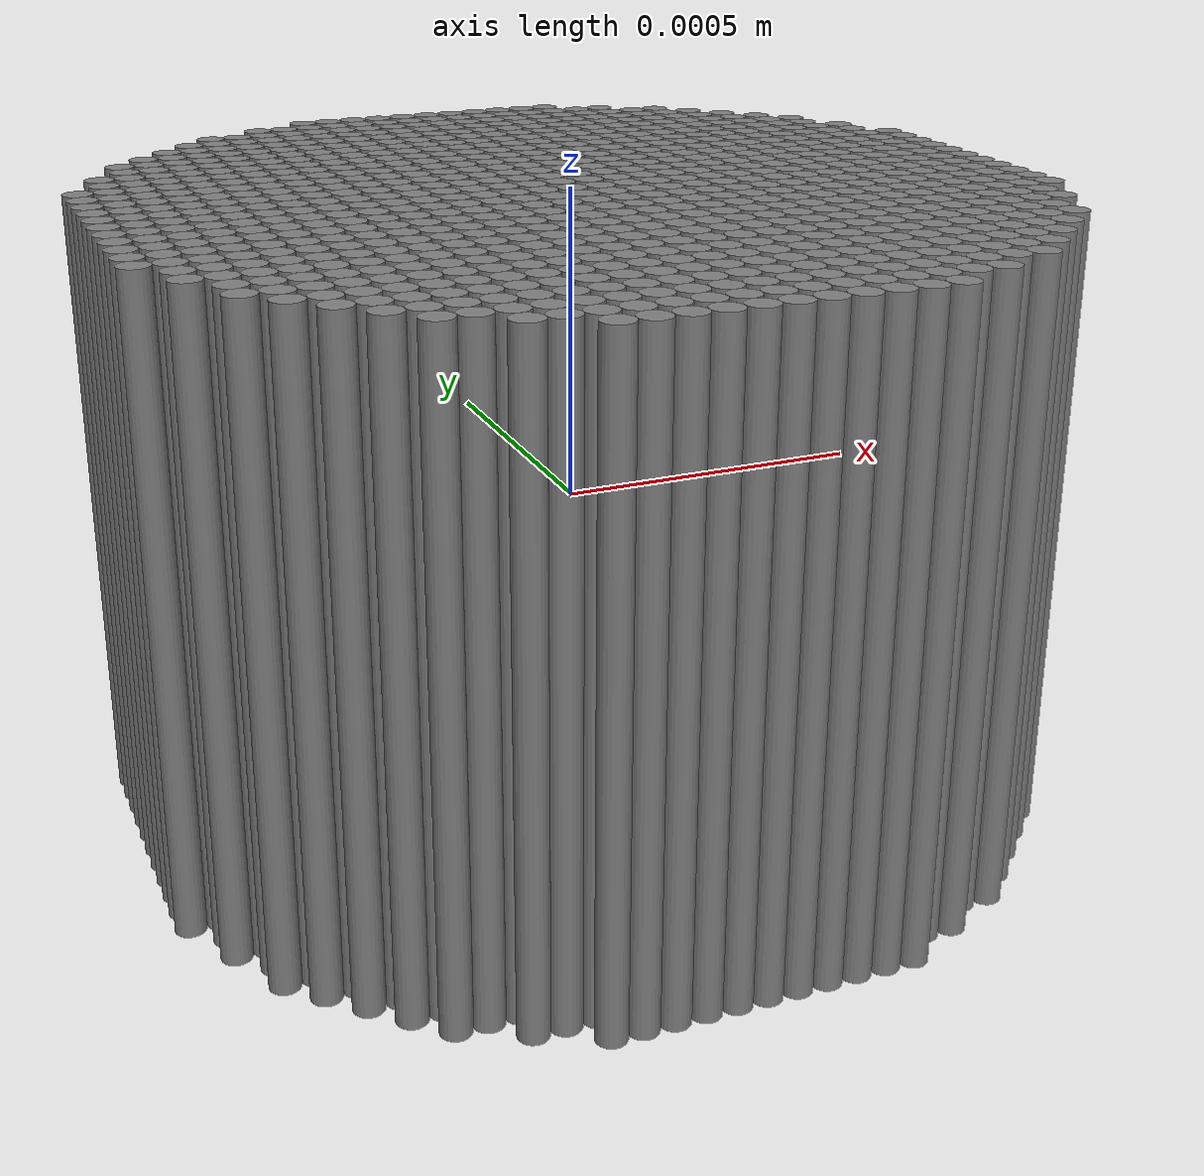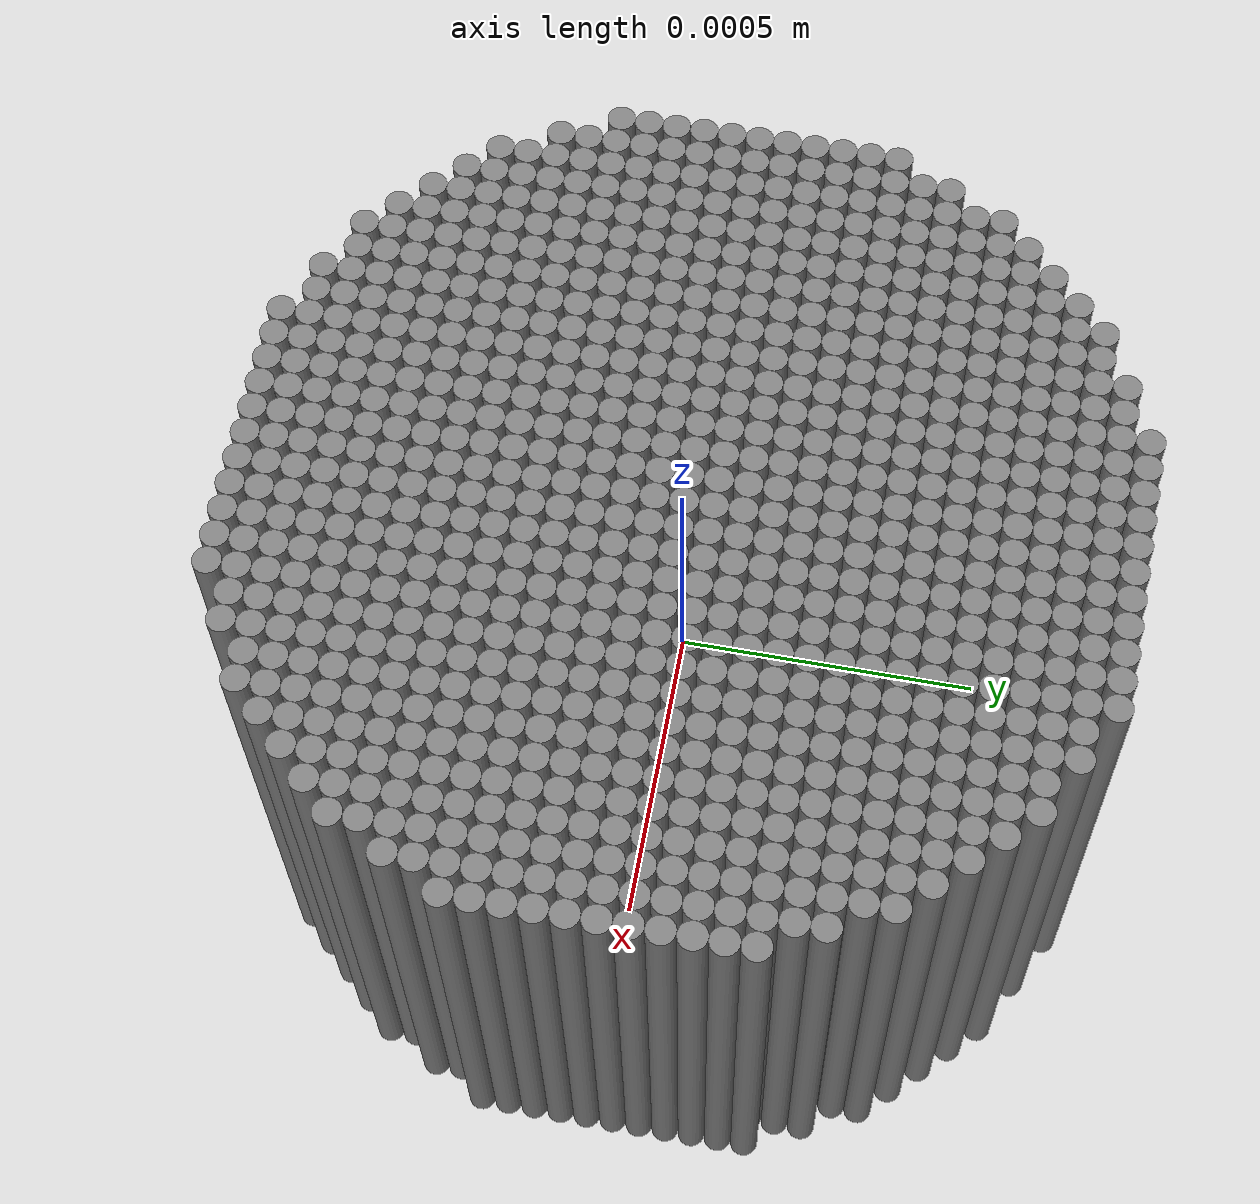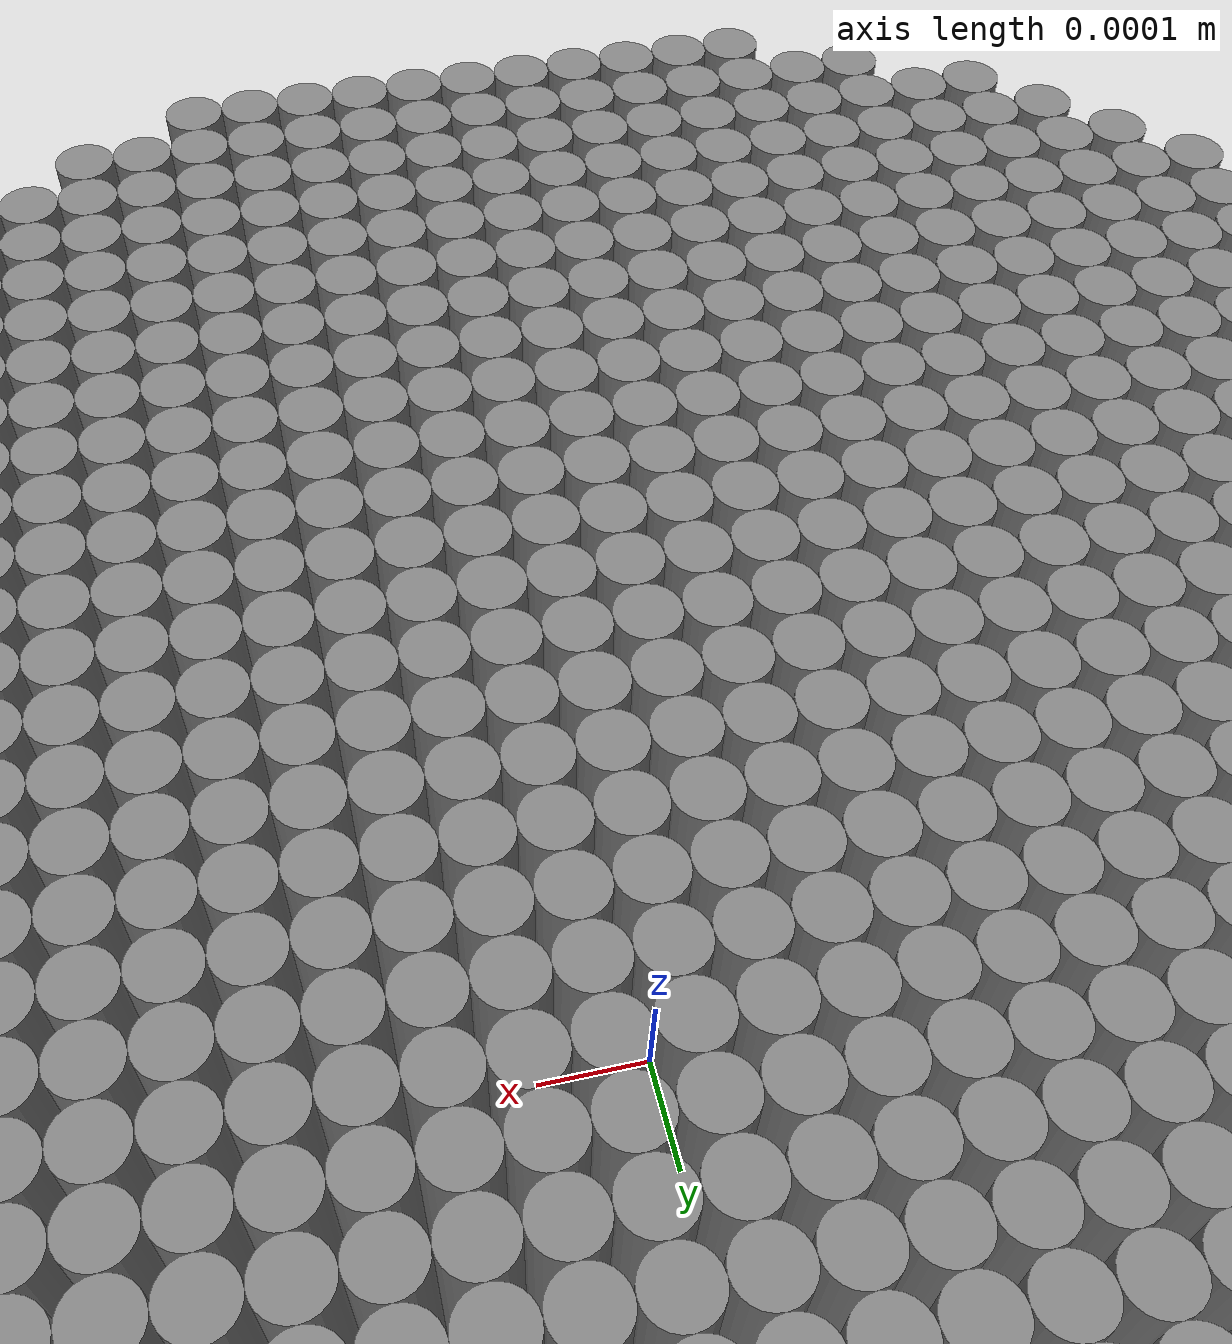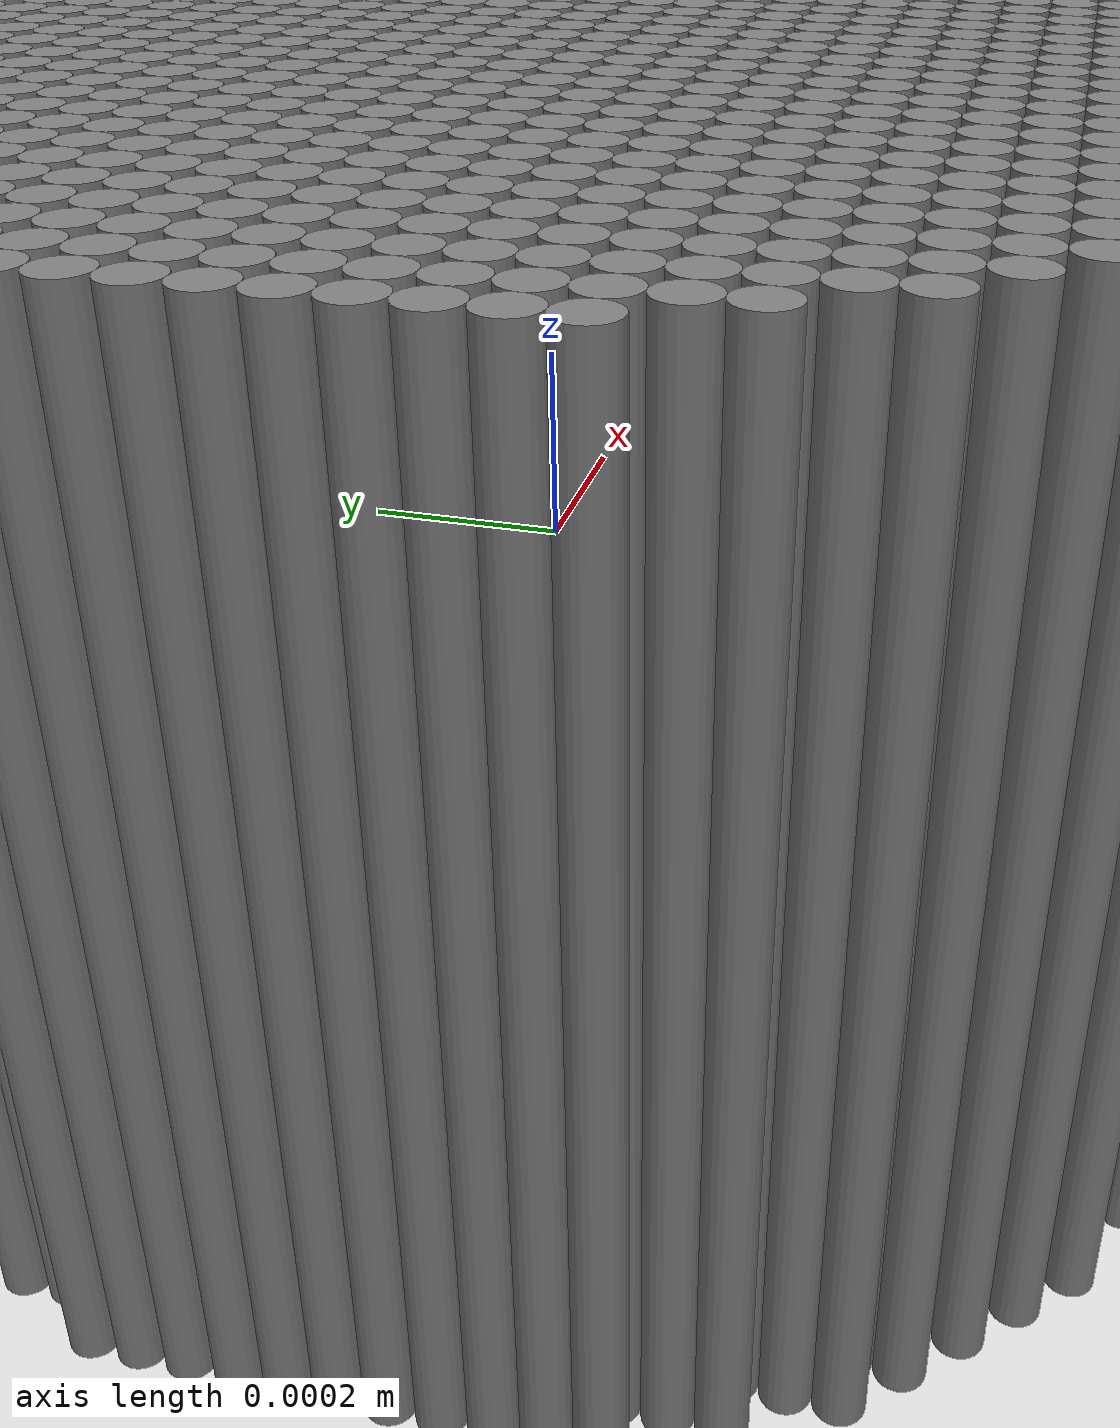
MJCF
<mujoco>
    <worldbody>

        <body pos='0 0 0' name='base-dot'>
            <geom type='cylinder' size='2.349964007466563e-05 0.0005' pos='-0.0002330079183573558 -0.0007030007198506687 0'/>
            <geom type='cylinder' size='2.349964007466563e-05 0.0005' pos='-0.0001860086382080245 -0.0007030007198506687 0'/>
            <geom type='cylinder' size='2.349964007466563e-05 0.0005' pos='-0.0001390093580586932 -0.0007030007198506687 0'/>
            <geom type='cylinder' size='2.349964007466563e-05 0.0005' pos='-9.201007790936191e-05 -0.0007030007198506687 0'/>
            <geom type='cylinder' size='2.349964007466563e-05 0.0005' pos='-4.501079776003062e-05 -0.0007030007198506687 0'/>
            <geom type='cylinder' size='2.349964007466563e-05 0.0005' pos='1.988482389300673e-06 -0.0007030007198506687 0'/>
            <geom type='cylinder' size='2.349964007466563e-05 0.0005' pos='4.8987762538631966e-05 -0.0007030007198506687 0'/>
            <geom type='cylinder' size='2.349964007466563e-05 0.0005' pos='9.598704268796326e-05 -0.0007030007198506687 0'/>
            <geom type='cylinder' size='2.349964007466563e-05 0.0005' pos='0.00014298632283729455 -0.0007030007198506687 0'/>
            <geom type='cylinder' size='2.349964007466563e-05 0.0005' pos='0.00018998560298662585 -0.0007030007198506687 0'/>
            <geom type='cylinder' size='2.349964007466563e-05 0.0005' pos='0.00023698488313595714 -0.0007030007198506687 0'/>
            <geom type='cylinder' size='2.349964007466563e-05 0.0005' pos='-0.0003270064786560184 -0.0006560014397013374 0'/>
            <geom type='cylinder' size='2.349964007466563e-05 0.0005' pos='-0.0002800071985066871 -0.0006560014397013374 0'/>
            <geom type='cylinder' size='2.349964007466563e-05 0.0005' pos='-0.0002330079183573558 -0.0006560014397013374 0'/>
            <geom type='cylinder' size='2.349964007466563e-05 0.0005' pos='-0.0001860086382080245 -0.0006560014397013374 0'/>
            <geom type='cylinder' size='2.349964007466563e-05 0.0005' pos='-0.0001390093580586932 -0.0006560014397013374 0'/>
            <geom type='cylinder' size='2.349964007466563e-05 0.0005' pos='-9.201007790936191e-05 -0.0006560014397013374 0'/>
            <geom type='cylinder' size='2.349964007466563e-05 0.0005' pos='-4.501079776003062e-05 -0.0006560014397013374 0'/>
            <geom type='cylinder' size='2.349964007466563e-05 0.0005' pos='1.988482389300673e-06 -0.0006560014397013374 0'/>
            <geom type='cylinder' size='2.349964007466563e-05 0.0005' pos='4.8987762538631966e-05 -0.0006560014397013374 0'/>
            <geom type='cylinder' size='2.349964007466563e-05 0.0005' pos='9.598704268796326e-05 -0.0006560014397013374 0'/>
            <geom type='cylinder' size='2.349964007466563e-05 0.0005' pos='0.00014298632283729455 -0.0006560014397013374 0'/>
            <geom type='cylinder' size='2.349964007466563e-05 0.0005' pos='0.00018998560298662585 -0.0006560014397013374 0'/>
            <geom type='cylinder' size='2.349964007466563e-05 0.0005' pos='0.00023698488313595714 -0.0006560014397013374 0'/>
            <geom type='cylinder' size='2.349964007466563e-05 0.0005' pos='0.00028398416328528843 -0.0006560014397013374 0'/>
            <geom type='cylinder' size='2.349964007466563e-05 0.0005' pos='0.0003309834434346197 -0.0006560014397013374 0'/>
            <geom type='cylinder' size='2.349964007466563e-05 0.0005' pos='-0.00042100503895468096 -0.0006090021595520061 0'/>
            <geom type='cylinder' size='2.349964007466563e-05 0.0005' pos='-0.00037400575880534967 -0.0006090021595520061 0'/>
            <geom type='cylinder' size='2.349964007466563e-05 0.0005' pos='-0.0003270064786560184 -0.0006090021595520061 0'/>
            <geom type='cylinder' size='2.349964007466563e-05 0.0005' pos='-0.0002800071985066871 -0.0006090021595520061 0'/>
            <geom type='cylinder' size='2.349964007466563e-05 0.0005' pos='-0.0002330079183573558 -0.0006090021595520061 0'/>
            <geom type='cylinder' size='2.349964007466563e-05 0.0005' pos='-0.0001860086382080245 -0.0006090021595520061 0'/>
            <geom type='cylinder' size='2.349964007466563e-05 0.0005' pos='-0.0001390093580586932 -0.0006090021595520061 0'/>
            <geom type='cylinder' size='2.349964007466563e-05 0.0005' pos='-9.201007790936191e-05 -0.0006090021595520061 0'/>
            <geom type='cylinder' size='2.349964007466563e-05 0.0005' pos='-4.501079776003062e-05 -0.0006090021595520061 0'/>
            <geom type='cylinder' size='2.349964007466563e-05 0.0005' pos='1.988482389300673e-06 -0.0006090021595520061 0'/>
            <geom type='cylinder' size='2.349964007466563e-05 0.0005' pos='4.8987762538631966e-05 -0.0006090021595520061 0'/>
            <geom type='cylinder' size='2.349964007466563e-05 0.0005' pos='9.598704268796326e-05 -0.0006090021595520061 0'/>
            <geom type='cylinder' size='2.349964007466563e-05 0.0005' pos='0.00014298632283729455 -0.0006090021595520061 0'/>
            <geom type='cylinder' size='2.349964007466563e-05 0.0005' pos='0.00018998560298662585 -0.0006090021595520061 0'/>
            <geom type='cylinder' size='2.349964007466563e-05 0.0005' pos='0.00023698488313595714 -0.0006090021595520061 0'/>
            <geom type='cylinder' size='2.349964007466563e-05 0.0005' pos='0.00028398416328528843 -0.0006090021595520061 0'/>
            <geom type='cylinder' size='2.349964007466563e-05 0.0005' pos='0.0003309834434346197 -0.0006090021595520061 0'/>
            <geom type='cylinder' size='2.349964007466563e-05 0.0005' pos='0.000377982723583951 -0.0006090021595520061 0'/>
            <geom type='cylinder' size='2.349964007466563e-05 0.0005' pos='0.0004249820037332823 -0.0006090021595520061 0'/>
            <geom type='cylinder' size='2.349964007466563e-05 0.0005' pos='-0.00046800431910401226 -0.0005620028794026748 0'/>
            <geom type='cylinder' size='2.349964007466563e-05 0.0005' pos='-0.00042100503895468096 -0.0005620028794026748 0'/>
            <geom type='cylinder' size='2.349964007466563e-05 0.0005' pos='-0.00037400575880534967 -0.0005620028794026748 0'/>
            <geom type='cylinder' size='2.349964007466563e-05 0.0005' pos='-0.0003270064786560184 -0.0005620028794026748 0'/>
            <geom type='cylinder' size='2.349964007466563e-05 0.0005' pos='-0.0002800071985066871 -0.0005620028794026748 0'/>
            <geom type='cylinder' size='2.349964007466563e-05 0.0005' pos='-0.0002330079183573558 -0.0005620028794026748 0'/>
            <geom type='cylinder' size='2.349964007466563e-05 0.0005' pos='-0.0001860086382080245 -0.0005620028794026748 0'/>
            <geom type='cylinder' size='2.349964007466563e-05 0.0005' pos='-0.0001390093580586932 -0.0005620028794026748 0'/>
            <geom type='cylinder' size='2.349964007466563e-05 0.0005' pos='-9.201007790936191e-05 -0.0005620028794026748 0'/>
            <geom type='cylinder' size='2.349964007466563e-05 0.0005' pos='-4.501079776003062e-05 -0.0005620028794026748 0'/>
            <geom type='cylinder' size='2.349964007466563e-05 0.0005' pos='1.988482389300673e-06 -0.0005620028794026748 0'/>
            <geom type='cylinder' size='2.349964007466563e-05 0.0005' pos='4.8987762538631966e-05 -0.0005620028794026748 0'/>
            <geom type='cylinder' size='2.349964007466563e-05 0.0005' pos='9.598704268796326e-05 -0.0005620028794026748 0'/>
            <geom type='cylinder' size='2.349964007466563e-05 0.0005' pos='0.00014298632283729455 -0.0005620028794026748 0'/>
            <geom type='cylinder' size='2.349964007466563e-05 0.0005' pos='0.00018998560298662585 -0.0005620028794026748 0'/>
            <geom type='cylinder' size='2.349964007466563e-05 0.0005' pos='0.00023698488313595714 -0.0005620028794026748 0'/>
            <geom type='cylinder' size='2.349964007466563e-05 0.0005' pos='0.00028398416328528843 -0.0005620028794026748 0'/>
            <geom type='cylinder' size='2.349964007466563e-05 0.0005' pos='0.0003309834434346197 -0.0005620028794026748 0'/>
            <geom type='cylinder' size='2.349964007466563e-05 0.0005' pos='0.000377982723583951 -0.0005620028794026748 0'/>
            <geom type='cylinder' size='2.349964007466563e-05 0.0005' pos='0.0004249820037332823 -0.0005620028794026748 0'/>
            <geom type='cylinder' size='2.349964007466563e-05 0.0005' pos='0.0004719812838826136 -0.0005620028794026748 0'/>
            <geom type='cylinder' size='2.349964007466563e-05 0.0005' pos='-0.0005150035992533436 -0.0005150035992533436 0'/>
            <geom type='cylinder' size='2.349964007466563e-05 0.0005' pos='-0.00046800431910401226 -0.0005150035992533436 0'/>
            <geom type='cylinder' size='2.349964007466563e-05 0.0005' pos='-0.00042100503895468096 -0.0005150035992533436 0'/>
            <geom type='cylinder' size='2.349964007466563e-05 0.0005' pos='-0.00037400575880534967 -0.0005150035992533436 0'/>
            <geom type='cylinder' size='2.349964007466563e-05 0.0005' pos='-0.0003270064786560184 -0.0005150035992533436 0'/>
            <geom type='cylinder' size='2.349964007466563e-05 0.0005' pos='-0.0002800071985066871 -0.0005150035992533436 0'/>
            <geom type='cylinder' size='2.349964007466563e-05 0.0005' pos='-0.0002330079183573558 -0.0005150035992533436 0'/>
            <geom type='cylinder' size='2.349964007466563e-05 0.0005' pos='-0.0001860086382080245 -0.0005150035992533436 0'/>
            <geom type='cylinder' size='2.349964007466563e-05 0.0005' pos='-0.0001390093580586932 -0.0005150035992533436 0'/>
            <geom type='cylinder' size='2.349964007466563e-05 0.0005' pos='-9.201007790936191e-05 -0.0005150035992533436 0'/>
            <geom type='cylinder' size='2.349964007466563e-05 0.0005' pos='-4.501079776003062e-05 -0.0005150035992533436 0'/>
            <geom type='cylinder' size='2.349964007466563e-05 0.0005' pos='1.988482389300673e-06 -0.0005150035992533436 0'/>
            <geom type='cylinder' size='2.349964007466563e-05 0.0005' pos='4.8987762538631966e-05 -0.0005150035992533436 0'/>
            <geom type='cylinder' size='2.349964007466563e-05 0.0005' pos='9.598704268796326e-05 -0.0005150035992533436 0'/>
            <geom type='cylinder' size='2.349964007466563e-05 0.0005' pos='0.00014298632283729455 -0.0005150035992533436 0'/>
            <geom type='cylinder' size='2.349964007466563e-05 0.0005' pos='0.00018998560298662585 -0.0005150035992533436 0'/>
            <geom type='cylinder' size='2.349964007466563e-05 0.0005' pos='0.00023698488313595714 -0.0005150035992533436 0'/>
            <geom type='cylinder' size='2.349964007466563e-05 0.0005' pos='0.00028398416328528843 -0.0005150035992533436 0'/>
            <geom type='cylinder' size='2.349964007466563e-05 0.0005' pos='0.0003309834434346197 -0.0005150035992533436 0'/>
            <geom type='cylinder' size='2.349964007466563e-05 0.0005' pos='0.000377982723583951 -0.0005150035992533436 0'/>
            <geom type='cylinder' size='2.349964007466563e-05 0.0005' pos='0.0004249820037332823 -0.0005150035992533436 0'/>
            <geom type='cylinder' size='2.349964007466563e-05 0.0005' pos='0.0004719812838826136 -0.0005150035992533436 0'/>
            <geom type='cylinder' size='2.349964007466563e-05 0.0005' pos='0.0005189805640319449 -0.0005150035992533436 0'/>
            <geom type='cylinder' size='2.349964007466563e-05 0.0005' pos='-0.0005620028794026748 -0.00046800431910401226 0'/>
            <geom type='cylinder' size='2.349964007466563e-05 0.0005' pos='-0.0005150035992533436 -0.00046800431910401226 0'/>
            <geom type='cylinder' size='2.349964007466563e-05 0.0005' pos='-0.00046800431910401226 -0.00046800431910401226 0'/>
            <geom type='cylinder' size='2.349964007466563e-05 0.0005' pos='-0.00042100503895468096 -0.00046800431910401226 0'/>
            <geom type='cylinder' size='2.349964007466563e-05 0.0005' pos='-0.00037400575880534967 -0.00046800431910401226 0'/>
            <geom type='cylinder' size='2.349964007466563e-05 0.0005' pos='-0.0003270064786560184 -0.00046800431910401226 0'/>
            <geom type='cylinder' size='2.349964007466563e-05 0.0005' pos='-0.0002800071985066871 -0.00046800431910401226 0'/>
            <geom type='cylinder' size='2.349964007466563e-05 0.0005' pos='-0.0002330079183573558 -0.00046800431910401226 0'/>
            <geom type='cylinder' size='2.349964007466563e-05 0.0005' pos='-0.0001860086382080245 -0.00046800431910401226 0'/>
            <geom type='cylinder' size='2.349964007466563e-05 0.0005' pos='-0.0001390093580586932 -0.00046800431910401226 0'/>
            <geom type='cylinder' size='2.349964007466563e-05 0.0005' pos='-9.201007790936191e-05 -0.00046800431910401226 0'/>
            <geom type='cylinder' size='2.349964007466563e-05 0.0005' pos='-4.501079776003062e-05 -0.00046800431910401226 0'/>
            <geom type='cylinder' size='2.349964007466563e-05 0.0005' pos='1.988482389300673e-06 -0.00046800431910401226 0'/>
            <geom type='cylinder' size='2.349964007466563e-05 0.0005' pos='4.8987762538631966e-05 -0.00046800431910401226 0'/>
            <geom type='cylinder' size='2.349964007466563e-05 0.0005' pos='9.598704268796326e-05 -0.00046800431910401226 0'/>
            <geom type='cylinder' size='2.349964007466563e-05 0.0005' pos='0.00014298632283729455 -0.00046800431910401226 0'/>
            <geom type='cylinder' size='2.349964007466563e-05 0.0005' pos='0.00018998560298662585 -0.00046800431910401226 0'/>
            <geom type='cylinder' size='2.349964007466563e-05 0.0005' pos='0.00023698488313595714 -0.00046800431910401226 0'/>
            <geom type='cylinder' size='2.349964007466563e-05 0.0005' pos='0.00028398416328528843 -0.00046800431910401226 0'/>
            <geom type='cylinder' size='2.349964007466563e-05 0.0005' pos='0.0003309834434346197 -0.00046800431910401226 0'/>
            <geom type='cylinder' size='2.349964007466563e-05 0.0005' pos='0.000377982723583951 -0.00046800431910401226 0'/>
            <geom type='cylinder' size='2.349964007466563e-05 0.0005' pos='0.0004249820037332823 -0.00046800431910401226 0'/>
            <geom type='cylinder' size='2.349964007466563e-05 0.0005' pos='0.0004719812838826136 -0.00046800431910401226 0'/>
            <geom type='cylinder' size='2.349964007466563e-05 0.0005' pos='0.0005189805640319449 -0.00046800431910401226 0'/>
            <geom type='cylinder' size='2.349964007466563e-05 0.0005' pos='0.0005659798441812762 -0.00046800431910401226 0'/>
            <geom type='cylinder' size='2.349964007466563e-05 0.0005' pos='-0.0006090021595520061 -0.00042100503895468096 0'/>
            <geom type='cylinder' size='2.349964007466563e-05 0.0005' pos='-0.0005620028794026748 -0.00042100503895468096 0'/>
            <geom type='cylinder' size='2.349964007466563e-05 0.0005' pos='-0.0005150035992533436 -0.00042100503895468096 0'/>
            <geom type='cylinder' size='2.349964007466563e-05 0.0005' pos='-0.00046800431910401226 -0.00042100503895468096 0'/>
            <geom type='cylinder' size='2.349964007466563e-05 0.0005' pos='-0.00042100503895468096 -0.00042100503895468096 0'/>
            <geom type='cylinder' size='2.349964007466563e-05 0.0005' pos='-0.00037400575880534967 -0.00042100503895468096 0'/>
            <geom type='cylinder' size='2.349964007466563e-05 0.0005' pos='-0.0003270064786560184 -0.00042100503895468096 0'/>
            <geom type='cylinder' size='2.349964007466563e-05 0.0005' pos='-0.0002800071985066871 -0.00042100503895468096 0'/>
            <geom type='cylinder' size='2.349964007466563e-05 0.0005' pos='-0.0002330079183573558 -0.00042100503895468096 0'/>
            <geom type='cylinder' size='2.349964007466563e-05 0.0005' pos='-0.0001860086382080245 -0.00042100503895468096 0'/>
            <geom type='cylinder' size='2.349964007466563e-05 0.0005' pos='-0.0001390093580586932 -0.00042100503895468096 0'/>
            <geom type='cylinder' size='2.349964007466563e-05 0.0005' pos='-9.201007790936191e-05 -0.00042100503895468096 0'/>
            <geom type='cylinder' size='2.349964007466563e-05 0.0005' pos='-4.501079776003062e-05 -0.00042100503895468096 0'/>
            <geom type='cylinder' size='2.349964007466563e-05 0.0005' pos='1.988482389300673e-06 -0.00042100503895468096 0'/>
            <geom type='cylinder' size='2.349964007466563e-05 0.0005' pos='4.8987762538631966e-05 -0.00042100503895468096 0'/>
            <geom type='cylinder' size='2.349964007466563e-05 0.0005' pos='9.598704268796326e-05 -0.00042100503895468096 0'/>
            <geom type='cylinder' size='2.349964007466563e-05 0.0005' pos='0.00014298632283729455 -0.00042100503895468096 0'/>
            <geom type='cylinder' size='2.349964007466563e-05 0.0005' pos='0.00018998560298662585 -0.00042100503895468096 0'/>
            <geom type='cylinder' size='2.349964007466563e-05 0.0005' pos='0.00023698488313595714 -0.00042100503895468096 0'/>
            <geom type='cylinder' size='2.349964007466563e-05 0.0005' pos='0.00028398416328528843 -0.00042100503895468096 0'/>
            <geom type='cylinder' size='2.349964007466563e-05 0.0005' pos='0.0003309834434346197 -0.00042100503895468096 0'/>
            <geom type='cylinder' size='2.349964007466563e-05 0.0005' pos='0.000377982723583951 -0.00042100503895468096 0'/>
            <geom type='cylinder' size='2.349964007466563e-05 0.0005' pos='0.0004249820037332823 -0.00042100503895468096 0'/>
            <geom type='cylinder' size='2.349964007466563e-05 0.0005' pos='0.0004719812838826136 -0.00042100503895468096 0'/>
            <geom type='cylinder' size='2.349964007466563e-05 0.0005' pos='0.0005189805640319449 -0.00042100503895468096 0'/>
            <geom type='cylinder' size='2.349964007466563e-05 0.0005' pos='0.0005659798441812762 -0.00042100503895468096 0'/>
            <geom type='cylinder' size='2.349964007466563e-05 0.0005' pos='0.0006129791243306075 -0.00042100503895468096 0'/>
            <geom type='cylinder' size='2.349964007466563e-05 0.0005' pos='-0.0006090021595520061 -0.00037400575880534967 0'/>
            <geom type='cylinder' size='2.349964007466563e-05 0.0005' pos='-0.0005620028794026748 -0.00037400575880534967 0'/>
            <geom type='cylinder' size='2.349964007466563e-05 0.0005' pos='-0.0005150035992533436 -0.00037400575880534967 0'/>
            <geom type='cylinder' size='2.349964007466563e-05 0.0005' pos='-0.00046800431910401226 -0.00037400575880534967 0'/>
            <geom type='cylinder' size='2.349964007466563e-05 0.0005' pos='-0.00042100503895468096 -0.00037400575880534967 0'/>
            <geom type='cylinder' size='2.349964007466563e-05 0.0005' pos='-0.00037400575880534967 -0.00037400575880534967 0'/>
            <geom type='cylinder' size='2.349964007466563e-05 0.0005' pos='-0.0003270064786560184 -0.00037400575880534967 0'/>
            <geom type='cylinder' size='2.349964007466563e-05 0.0005' pos='-0.0002800071985066871 -0.00037400575880534967 0'/>
            <geom type='cylinder' size='2.349964007466563e-05 0.0005' pos='-0.0002330079183573558 -0.00037400575880534967 0'/>
            <geom type='cylinder' size='2.349964007466563e-05 0.0005' pos='-0.0001860086382080245 -0.00037400575880534967 0'/>
            <geom type='cylinder' size='2.349964007466563e-05 0.0005' pos='-0.0001390093580586932 -0.00037400575880534967 0'/>
            <geom type='cylinder' size='2.349964007466563e-05 0.0005' pos='-9.201007790936191e-05 -0.00037400575880534967 0'/>
            <geom type='cylinder' size='2.349964007466563e-05 0.0005' pos='-4.501079776003062e-05 -0.00037400575880534967 0'/>
            <geom type='cylinder' size='2.349964007466563e-05 0.0005' pos='1.988482389300673e-06 -0.00037400575880534967 0'/>
            <geom type='cylinder' size='2.349964007466563e-05 0.0005' pos='4.8987762538631966e-05 -0.00037400575880534967 0'/>
            <geom type='cylinder' size='2.349964007466563e-05 0.0005' pos='9.598704268796326e-05 -0.00037400575880534967 0'/>
            <geom type='cylinder' size='2.349964007466563e-05 0.0005' pos='0.00014298632283729455 -0.00037400575880534967 0'/>
            <geom type='cylinder' size='2.349964007466563e-05 0.0005' pos='0.00018998560298662585 -0.00037400575880534967 0'/>
            <geom type='cylinder' size='2.349964007466563e-05 0.0005' pos='0.00023698488313595714 -0.00037400575880534967 0'/>
            <geom type='cylinder' size='2.349964007466563e-05 0.0005' pos='0.00028398416328528843 -0.00037400575880534967 0'/>
            <geom type='cylinder' size='2.349964007466563e-05 0.0005' pos='0.0003309834434346197 -0.00037400575880534967 0'/>
            <geom type='cylinder' size='2.349964007466563e-05 0.0005' pos='0.000377982723583951 -0.00037400575880534967 0'/>
            <geom type='cylinder' size='2.349964007466563e-05 0.0005' pos='0.0004249820037332823 -0.00037400575880534967 0'/>
            <geom type='cylinder' size='2.349964007466563e-05 0.0005' pos='0.0004719812838826136 -0.00037400575880534967 0'/>
            <geom type='cylinder' size='2.349964007466563e-05 0.0005' pos='0.0005189805640319449 -0.00037400575880534967 0'/>
            <geom type='cylinder' size='2.349964007466563e-05 0.0005' pos='0.0005659798441812762 -0.00037400575880534967 0'/>
            <geom type='cylinder' size='2.349964007466563e-05 0.0005' pos='0.0006129791243306075 -0.00037400575880534967 0'/>
            <geom type='cylinder' size='2.349964007466563e-05 0.0005' pos='-0.0006560014397013374 -0.0003270064786560184 0'/>
            <geom type='cylinder' size='2.349964007466563e-05 0.0005' pos='-0.0006090021595520061 -0.0003270064786560184 0'/>
            <geom type='cylinder' size='2.349964007466563e-05 0.0005' pos='-0.0005620028794026748 -0.0003270064786560184 0'/>
            <geom type='cylinder' size='2.349964007466563e-05 0.0005' pos='-0.0005150035992533436 -0.0003270064786560184 0'/>
            <geom type='cylinder' size='2.349964007466563e-05 0.0005' pos='-0.00046800431910401226 -0.0003270064786560184 0'/>
            <geom type='cylinder' size='2.349964007466563e-05 0.0005' pos='-0.00042100503895468096 -0.0003270064786560184 0'/>
            <geom type='cylinder' size='2.349964007466563e-05 0.0005' pos='-0.00037400575880534967 -0.0003270064786560184 0'/>
            <geom type='cylinder' size='2.349964007466563e-05 0.0005' pos='-0.0003270064786560184 -0.0003270064786560184 0'/>
            <geom type='cylinder' size='2.349964007466563e-05 0.0005' pos='-0.0002800071985066871 -0.0003270064786560184 0'/>
            <geom type='cylinder' size='2.349964007466563e-05 0.0005' pos='-0.0002330079183573558 -0.0003270064786560184 0'/>
            <geom type='cylinder' size='2.349964007466563e-05 0.0005' pos='-0.0001860086382080245 -0.0003270064786560184 0'/>
            <geom type='cylinder' size='2.349964007466563e-05 0.0005' pos='-0.0001390093580586932 -0.0003270064786560184 0'/>
            <geom type='cylinder' size='2.349964007466563e-05 0.0005' pos='-9.201007790936191e-05 -0.0003270064786560184 0'/>
            <geom type='cylinder' size='2.349964007466563e-05 0.0005' pos='-4.501079776003062e-05 -0.0003270064786560184 0'/>
            <geom type='cylinder' size='2.349964007466563e-05 0.0005' pos='1.988482389300673e-06 -0.0003270064786560184 0'/>
            <geom type='cylinder' size='2.349964007466563e-05 0.0005' pos='4.8987762538631966e-05 -0.0003270064786560184 0'/>
            <geom type='cylinder' size='2.349964007466563e-05 0.0005' pos='9.598704268796326e-05 -0.0003270064786560184 0'/>
            <geom type='cylinder' size='2.349964007466563e-05 0.0005' pos='0.00014298632283729455 -0.0003270064786560184 0'/>
            <geom type='cylinder' size='2.349964007466563e-05 0.0005' pos='0.00018998560298662585 -0.0003270064786560184 0'/>
            <geom type='cylinder' size='2.349964007466563e-05 0.0005' pos='0.00023698488313595714 -0.0003270064786560184 0'/>
            <geom type='cylinder' size='2.349964007466563e-05 0.0005' pos='0.00028398416328528843 -0.0003270064786560184 0'/>
            <geom type='cylinder' size='2.349964007466563e-05 0.0005' pos='0.0003309834434346197 -0.0003270064786560184 0'/>
            <geom type='cylinder' size='2.349964007466563e-05 0.0005' pos='0.000377982723583951 -0.0003270064786560184 0'/>
            <geom type='cylinder' size='2.349964007466563e-05 0.0005' pos='0.0004249820037332823 -0.0003270064786560184 0'/>
            <geom type='cylinder' size='2.349964007466563e-05 0.0005' pos='0.0004719812838826136 -0.0003270064786560184 0'/>
            <geom type='cylinder' size='2.349964007466563e-05 0.0005' pos='0.0005189805640319449 -0.0003270064786560184 0'/>
            <geom type='cylinder' size='2.349964007466563e-05 0.0005' pos='0.0005659798441812762 -0.0003270064786560184 0'/>
            <geom type='cylinder' size='2.349964007466563e-05 0.0005' pos='0.0006129791243306075 -0.0003270064786560184 0'/>
            <geom type='cylinder' size='2.349964007466563e-05 0.0005' pos='0.0006599784044799388 -0.0003270064786560184 0'/>
            <geom type='cylinder' size='2.349964007466563e-05 0.0005' pos='-0.0006560014397013374 -0.0002800071985066871 0'/>
            <geom type='cylinder' size='2.349964007466563e-05 0.0005' pos='-0.0006090021595520061 -0.0002800071985066871 0'/>
            <geom type='cylinder' size='2.349964007466563e-05 0.0005' pos='-0.0005620028794026748 -0.0002800071985066871 0'/>
            <geom type='cylinder' size='2.349964007466563e-05 0.0005' pos='-0.0005150035992533436 -0.0002800071985066871 0'/>
            <geom type='cylinder' size='2.349964007466563e-05 0.0005' pos='-0.00046800431910401226 -0.0002800071985066871 0'/>
            <geom type='cylinder' size='2.349964007466563e-05 0.0005' pos='-0.00042100503895468096 -0.0002800071985066871 0'/>
            <geom type='cylinder' size='2.349964007466563e-05 0.0005' pos='-0.00037400575880534967 -0.0002800071985066871 0'/>
            <geom type='cylinder' size='2.349964007466563e-05 0.0005' pos='-0.0003270064786560184 -0.0002800071985066871 0'/>
            <geom type='cylinder' size='2.349964007466563e-05 0.0005' pos='-0.0002800071985066871 -0.0002800071985066871 0'/>
            <geom type='cylinder' size='2.349964007466563e-05 0.0005' pos='-0.0002330079183573558 -0.0002800071985066871 0'/>
            <geom type='cylinder' size='2.349964007466563e-05 0.0005' pos='-0.0001860086382080245 -0.0002800071985066871 0'/>
            <geom type='cylinder' size='2.349964007466563e-05 0.0005' pos='-0.0001390093580586932 -0.0002800071985066871 0'/>
            <geom type='cylinder' size='2.349964007466563e-05 0.0005' pos='-9.201007790936191e-05 -0.0002800071985066871 0'/>
            <geom type='cylinder' size='2.349964007466563e-05 0.0005' pos='-4.501079776003062e-05 -0.0002800071985066871 0'/>
            <geom type='cylinder' size='2.349964007466563e-05 0.0005' pos='1.988482389300673e-06 -0.0002800071985066871 0'/>
            <geom type='cylinder' size='2.349964007466563e-05 0.0005' pos='4.8987762538631966e-05 -0.0002800071985066871 0'/>
            <geom type='cylinder' size='2.349964007466563e-05 0.0005' pos='9.598704268796326e-05 -0.0002800071985066871 0'/>
            <geom type='cylinder' size='2.349964007466563e-05 0.0005' pos='0.00014298632283729455 -0.0002800071985066871 0'/>
            <geom type='cylinder' size='2.349964007466563e-05 0.0005' pos='0.00018998560298662585 -0.0002800071985066871 0'/>
            <geom type='cylinder' size='2.349964007466563e-05 0.0005' pos='0.00023698488313595714 -0.0002800071985066871 0'/>
            <geom type='cylinder' size='2.349964007466563e-05 0.0005' pos='0.00028398416328528843 -0.0002800071985066871 0'/>
            <geom type='cylinder' size='2.349964007466563e-05 0.0005' pos='0.0003309834434346197 -0.0002800071985066871 0'/>
            <geom type='cylinder' size='2.349964007466563e-05 0.0005' pos='0.000377982723583951 -0.0002800071985066871 0'/>
            <geom type='cylinder' size='2.349964007466563e-05 0.0005' pos='0.0004249820037332823 -0.0002800071985066871 0'/>
            <geom type='cylinder' size='2.349964007466563e-05 0.0005' pos='0.0004719812838826136 -0.0002800071985066871 0'/>
            <geom type='cylinder' size='2.349964007466563e-05 0.0005' pos='0.0005189805640319449 -0.0002800071985066871 0'/>
            <geom type='cylinder' size='2.349964007466563e-05 0.0005' pos='0.0005659798441812762 -0.0002800071985066871 0'/>
            <geom type='cylinder' size='2.349964007466563e-05 0.0005' pos='0.0006129791243306075 -0.0002800071985066871 0'/>
            <geom type='cylinder' size='2.349964007466563e-05 0.0005' pos='0.0006599784044799388 -0.0002800071985066871 0'/>
            <geom type='cylinder' size='2.349964007466563e-05 0.0005' pos='-0.0007030007198506687 -0.0002330079183573558 0'/>
            <geom type='cylinder' size='2.349964007466563e-05 0.0005' pos='-0.0006560014397013374 -0.0002330079183573558 0'/>
            <geom type='cylinder' size='2.349964007466563e-05 0.0005' pos='-0.0006090021595520061 -0.0002330079183573558 0'/>
            <geom type='cylinder' size='2.349964007466563e-05 0.0005' pos='-0.0005620028794026748 -0.0002330079183573558 0'/>
            <geom type='cylinder' size='2.349964007466563e-05 0.0005' pos='-0.0005150035992533436 -0.0002330079183573558 0'/>
            <geom type='cylinder' size='2.349964007466563e-05 0.0005' pos='-0.00046800431910401226 -0.0002330079183573558 0'/>
            <geom type='cylinder' size='2.349964007466563e-05 0.0005' pos='-0.00042100503895468096 -0.0002330079183573558 0'/>
            <geom type='cylinder' size='2.349964007466563e-05 0.0005' pos='-0.00037400575880534967 -0.0002330079183573558 0'/>
            <geom type='cylinder' size='2.349964007466563e-05 0.0005' pos='-0.0003270064786560184 -0.0002330079183573558 0'/>
            <geom type='cylinder' size='2.349964007466563e-05 0.0005' pos='-0.0002800071985066871 -0.0002330079183573558 0'/>
            <geom type='cylinder' size='2.349964007466563e-05 0.0005' pos='-0.0002330079183573558 -0.0002330079183573558 0'/>
            <geom type='cylinder' size='2.349964007466563e-05 0.0005' pos='-0.0001860086382080245 -0.0002330079183573558 0'/>
            <geom type='cylinder' size='2.349964007466563e-05 0.0005' pos='-0.0001390093580586932 -0.0002330079183573558 0'/>
            <geom type='cylinder' size='2.349964007466563e-05 0.0005' pos='-9.201007790936191e-05 -0.0002330079183573558 0'/>
            <geom type='cylinder' size='2.349964007466563e-05 0.0005' pos='-4.501079776003062e-05 -0.0002330079183573558 0'/>
            <geom type='cylinder' size='2.349964007466563e-05 0.0005' pos='1.988482389300673e-06 -0.0002330079183573558 0'/>
            <geom type='cylinder' size='2.349964007466563e-05 0.0005' pos='4.8987762538631966e-05 -0.0002330079183573558 0'/>
            <geom type='cylinder' size='2.349964007466563e-05 0.0005' pos='9.598704268796326e-05 -0.0002330079183573558 0'/>
            <geom type='cylinder' size='2.349964007466563e-05 0.0005' pos='0.00014298632283729455 -0.0002330079183573558 0'/>
            <geom type='cylinder' size='2.349964007466563e-05 0.0005' pos='0.00018998560298662585 -0.0002330079183573558 0'/>
            <geom type='cylinder' size='2.349964007466563e-05 0.0005' pos='0.00023698488313595714 -0.0002330079183573558 0'/>
            <geom type='cylinder' size='2.349964007466563e-05 0.0005' pos='0.00028398416328528843 -0.0002330079183573558 0'/>
            <geom type='cylinder' size='2.349964007466563e-05 0.0005' pos='0.0003309834434346197 -0.0002330079183573558 0'/>
            <geom type='cylinder' size='2.349964007466563e-05 0.0005' pos='0.000377982723583951 -0.0002330079183573558 0'/>
            <geom type='cylinder' size='2.349964007466563e-05 0.0005' pos='0.0004249820037332823 -0.0002330079183573558 0'/>
            <geom type='cylinder' size='2.349964007466563e-05 0.0005' pos='0.0004719812838826136 -0.0002330079183573558 0'/>
            <geom type='cylinder' size='2.349964007466563e-05 0.0005' pos='0.0005189805640319449 -0.0002330079183573558 0'/>
            <geom type='cylinder' size='2.349964007466563e-05 0.0005' pos='0.0005659798441812762 -0.0002330079183573558 0'/>
            <geom type='cylinder' size='2.349964007466563e-05 0.0005' pos='0.0006129791243306075 -0.0002330079183573558 0'/>
            <geom type='cylinder' size='2.349964007466563e-05 0.0005' pos='0.0006599784044799388 -0.0002330079183573558 0'/>
            <geom type='cylinder' size='2.349964007466563e-05 0.0005' pos='0.0007069776846292701 -0.0002330079183573558 0'/>
            <geom type='cylinder' size='2.349964007466563e-05 0.0005' pos='-0.0007030007198506687 -0.0001860086382080245 0'/>
            <geom type='cylinder' size='2.349964007466563e-05 0.0005' pos='-0.0006560014397013374 -0.0001860086382080245 0'/>
            <geom type='cylinder' size='2.349964007466563e-05 0.0005' pos='-0.0006090021595520061 -0.0001860086382080245 0'/>
            <geom type='cylinder' size='2.349964007466563e-05 0.0005' pos='-0.0005620028794026748 -0.0001860086382080245 0'/>
            <geom type='cylinder' size='2.349964007466563e-05 0.0005' pos='-0.0005150035992533436 -0.0001860086382080245 0'/>
            <geom type='cylinder' size='2.349964007466563e-05 0.0005' pos='-0.00046800431910401226 -0.0001860086382080245 0'/>
            <geom type='cylinder' size='2.349964007466563e-05 0.0005' pos='-0.00042100503895468096 -0.0001860086382080245 0'/>
            <geom type='cylinder' size='2.349964007466563e-05 0.0005' pos='-0.00037400575880534967 -0.0001860086382080245 0'/>
            <geom type='cylinder' size='2.349964007466563e-05 0.0005' pos='-0.0003270064786560184 -0.0001860086382080245 0'/>
            <geom type='cylinder' size='2.349964007466563e-05 0.0005' pos='-0.0002800071985066871 -0.0001860086382080245 0'/>
            <geom type='cylinder' size='2.349964007466563e-05 0.0005' pos='-0.0002330079183573558 -0.0001860086382080245 0'/>
            <geom type='cylinder' size='2.349964007466563e-05 0.0005' pos='-0.0001860086382080245 -0.0001860086382080245 0'/>
            <geom type='cylinder' size='2.349964007466563e-05 0.0005' pos='-0.0001390093580586932 -0.0001860086382080245 0'/>
            <geom type='cylinder' size='2.349964007466563e-05 0.0005' pos='-9.201007790936191e-05 -0.0001860086382080245 0'/>
            <geom type='cylinder' size='2.349964007466563e-05 0.0005' pos='-4.501079776003062e-05 -0.0001860086382080245 0'/>
            <geom type='cylinder' size='2.349964007466563e-05 0.0005' pos='1.988482389300673e-06 -0.0001860086382080245 0'/>
            <geom type='cylinder' size='2.349964007466563e-05 0.0005' pos='4.8987762538631966e-05 -0.0001860086382080245 0'/>
            <geom type='cylinder' size='2.349964007466563e-05 0.0005' pos='9.598704268796326e-05 -0.0001860086382080245 0'/>
            <geom type='cylinder' size='2.349964007466563e-05 0.0005' pos='0.00014298632283729455 -0.0001860086382080245 0'/>
            <geom type='cylinder' size='2.349964007466563e-05 0.0005' pos='0.00018998560298662585 -0.0001860086382080245 0'/>
            <geom type='cylinder' size='2.349964007466563e-05 0.0005' pos='0.00023698488313595714 -0.0001860086382080245 0'/>
            <geom type='cylinder' size='2.349964007466563e-05 0.0005' pos='0.00028398416328528843 -0.0001860086382080245 0'/>
            <geom type='cylinder' size='2.349964007466563e-05 0.0005' pos='0.0003309834434346197 -0.0001860086382080245 0'/>
            <geom type='cylinder' size='2.349964007466563e-05 0.0005' pos='0.000377982723583951 -0.0001860086382080245 0'/>
            <geom type='cylinder' size='2.349964007466563e-05 0.0005' pos='0.0004249820037332823 -0.0001860086382080245 0'/>
            <geom type='cylinder' size='2.349964007466563e-05 0.0005' pos='0.0004719812838826136 -0.0001860086382080245 0'/>
            <geom type='cylinder' size='2.349964007466563e-05 0.0005' pos='0.0005189805640319449 -0.0001860086382080245 0'/>
            <geom type='cylinder' size='2.349964007466563e-05 0.0005' pos='0.0005659798441812762 -0.0001860086382080245 0'/>
            <geom type='cylinder' size='2.349964007466563e-05 0.0005' pos='0.0006129791243306075 -0.0001860086382080245 0'/>
            <geom type='cylinder' size='2.349964007466563e-05 0.0005' pos='0.0006599784044799388 -0.0001860086382080245 0'/>
            <geom type='cylinder' size='2.349964007466563e-05 0.0005' pos='0.0007069776846292701 -0.0001860086382080245 0'/>
            <geom type='cylinder' size='2.349964007466563e-05 0.0005' pos='-0.0007030007198506687 -0.0001390093580586932 0'/>
            <geom type='cylinder' size='2.349964007466563e-05 0.0005' pos='-0.0006560014397013374 -0.0001390093580586932 0'/>
            <geom type='cylinder' size='2.349964007466563e-05 0.0005' pos='-0.0006090021595520061 -0.0001390093580586932 0'/>
            <geom type='cylinder' size='2.349964007466563e-05 0.0005' pos='-0.0005620028794026748 -0.0001390093580586932 0'/>
            <geom type='cylinder' size='2.349964007466563e-05 0.0005' pos='-0.0005150035992533436 -0.0001390093580586932 0'/>
            <geom type='cylinder' size='2.349964007466563e-05 0.0005' pos='-0.00046800431910401226 -0.0001390093580586932 0'/>
            <geom type='cylinder' size='2.349964007466563e-05 0.0005' pos='-0.00042100503895468096 -0.0001390093580586932 0'/>
            <geom type='cylinder' size='2.349964007466563e-05 0.0005' pos='-0.00037400575880534967 -0.0001390093580586932 0'/>
            <geom type='cylinder' size='2.349964007466563e-05 0.0005' pos='-0.0003270064786560184 -0.0001390093580586932 0'/>
            <geom type='cylinder' size='2.349964007466563e-05 0.0005' pos='-0.0002800071985066871 -0.0001390093580586932 0'/>
            <geom type='cylinder' size='2.349964007466563e-05 0.0005' pos='-0.0002330079183573558 -0.0001390093580586932 0'/>
            <geom type='cylinder' size='2.349964007466563e-05 0.0005' pos='-0.0001860086382080245 -0.0001390093580586932 0'/>
            <geom type='cylinder' size='2.349964007466563e-05 0.0005' pos='-0.0001390093580586932 -0.0001390093580586932 0'/>
            <geom type='cylinder' size='2.349964007466563e-05 0.0005' pos='-9.201007790936191e-05 -0.0001390093580586932 0'/>
            <geom type='cylinder' size='2.349964007466563e-05 0.0005' pos='-4.501079776003062e-05 -0.0001390093580586932 0'/>
            <geom type='cylinder' size='2.349964007466563e-05 0.0005' pos='1.988482389300673e-06 -0.0001390093580586932 0'/>
            <geom type='cylinder' size='2.349964007466563e-05 0.0005' pos='4.8987762538631966e-05 -0.0001390093580586932 0'/>
            <geom type='cylinder' size='2.349964007466563e-05 0.0005' pos='9.598704268796326e-05 -0.0001390093580586932 0'/>
            <geom type='cylinder' size='2.349964007466563e-05 0.0005' pos='0.00014298632283729455 -0.0001390093580586932 0'/>
            <geom type='cylinder' size='2.349964007466563e-05 0.0005' pos='0.00018998560298662585 -0.0001390093580586932 0'/>
            <geom type='cylinder' size='2.349964007466563e-05 0.0005' pos='0.00023698488313595714 -0.0001390093580586932 0'/>
            <geom type='cylinder' size='2.349964007466563e-05 0.0005' pos='0.00028398416328528843 -0.0001390093580586932 0'/>
            <geom type='cylinder' size='2.349964007466563e-05 0.0005' pos='0.0003309834434346197 -0.0001390093580586932 0'/>
            <geom type='cylinder' size='2.349964007466563e-05 0.0005' pos='0.000377982723583951 -0.0001390093580586932 0'/>
            <geom type='cylinder' size='2.349964007466563e-05 0.0005' pos='0.0004249820037332823 -0.0001390093580586932 0'/>
            <geom type='cylinder' size='2.349964007466563e-05 0.0005' pos='0.0004719812838826136 -0.0001390093580586932 0'/>
            <geom type='cylinder' size='2.349964007466563e-05 0.0005' pos='0.0005189805640319449 -0.0001390093580586932 0'/>
            <geom type='cylinder' size='2.349964007466563e-05 0.0005' pos='0.0005659798441812762 -0.0001390093580586932 0'/>
            <geom type='cylinder' size='2.349964007466563e-05 0.0005' pos='0.0006129791243306075 -0.0001390093580586932 0'/>
            <geom type='cylinder' size='2.349964007466563e-05 0.0005' pos='0.0006599784044799388 -0.0001390093580586932 0'/>
            <geom type='cylinder' size='2.349964007466563e-05 0.0005' pos='0.0007069776846292701 -0.0001390093580586932 0'/>
            <geom type='cylinder' size='2.349964007466563e-05 0.0005' pos='-0.0007030007198506687 -9.201007790936191e-05 0'/>
            <geom type='cylinder' size='2.349964007466563e-05 0.0005' pos='-0.0006560014397013374 -9.201007790936191e-05 0'/>
            <geom type='cylinder' size='2.349964007466563e-05 0.0005' pos='-0.0006090021595520061 -9.201007790936191e-05 0'/>
            <geom type='cylinder' size='2.349964007466563e-05 0.0005' pos='-0.0005620028794026748 -9.201007790936191e-05 0'/>
            <geom type='cylinder' size='2.349964007466563e-05 0.0005' pos='-0.0005150035992533436 -9.201007790936191e-05 0'/>
            <geom type='cylinder' size='2.349964007466563e-05 0.0005' pos='-0.00046800431910401226 -9.201007790936191e-05 0'/>
            <geom type='cylinder' size='2.349964007466563e-05 0.0005' pos='-0.00042100503895468096 -9.201007790936191e-05 0'/>
            <geom type='cylinder' size='2.349964007466563e-05 0.0005' pos='-0.00037400575880534967 -9.201007790936191e-05 0'/>
            <geom type='cylinder' size='2.349964007466563e-05 0.0005' pos='-0.0003270064786560184 -9.201007790936191e-05 0'/>
            <geom type='cylinder' size='2.349964007466563e-05 0.0005' pos='-0.0002800071985066871 -9.201007790936191e-05 0'/>
            <geom type='cylinder' size='2.349964007466563e-05 0.0005' pos='-0.0002330079183573558 -9.201007790936191e-05 0'/>
            <geom type='cylinder' size='2.349964007466563e-05 0.0005' pos='-0.0001860086382080245 -9.201007790936191e-05 0'/>
            <geom type='cylinder' size='2.349964007466563e-05 0.0005' pos='-0.0001390093580586932 -9.201007790936191e-05 0'/>
            <geom type='cylinder' size='2.349964007466563e-05 0.0005' pos='-9.201007790936191e-05 -9.201007790936191e-05 0'/>
            <geom type='cylinder' size='2.349964007466563e-05 0.0005' pos='-4.501079776003062e-05 -9.201007790936191e-05 0'/>
            <geom type='cylinder' size='2.349964007466563e-05 0.0005' pos='1.988482389300673e-06 -9.201007790936191e-05 0'/>
            <geom type='cylinder' size='2.349964007466563e-05 0.0005' pos='4.8987762538631966e-05 -9.201007790936191e-05 0'/>
            <geom type='cylinder' size='2.349964007466563e-05 0.0005' pos='9.598704268796326e-05 -9.201007790936191e-05 0'/>
            <geom type='cylinder' size='2.349964007466563e-05 0.0005' pos='0.00014298632283729455 -9.201007790936191e-05 0'/>
            <geom type='cylinder' size='2.349964007466563e-05 0.0005' pos='0.00018998560298662585 -9.201007790936191e-05 0'/>
            <geom type='cylinder' size='2.349964007466563e-05 0.0005' pos='0.00023698488313595714 -9.201007790936191e-05 0'/>
            <geom type='cylinder' size='2.349964007466563e-05 0.0005' pos='0.00028398416328528843 -9.201007790936191e-05 0'/>
            <geom type='cylinder' size='2.349964007466563e-05 0.0005' pos='0.0003309834434346197 -9.201007790936191e-05 0'/>
            <geom type='cylinder' size='2.349964007466563e-05 0.0005' pos='0.000377982723583951 -9.201007790936191e-05 0'/>
            <geom type='cylinder' size='2.349964007466563e-05 0.0005' pos='0.0004249820037332823 -9.201007790936191e-05 0'/>
            <geom type='cylinder' size='2.349964007466563e-05 0.0005' pos='0.0004719812838826136 -9.201007790936191e-05 0'/>
            <geom type='cylinder' size='2.349964007466563e-05 0.0005' pos='0.0005189805640319449 -9.201007790936191e-05 0'/>
            <geom type='cylinder' size='2.349964007466563e-05 0.0005' pos='0.0005659798441812762 -9.201007790936191e-05 0'/>
            <geom type='cylinder' size='2.349964007466563e-05 0.0005' pos='0.0006129791243306075 -9.201007790936191e-05 0'/>
            <geom type='cylinder' size='2.349964007466563e-05 0.0005' pos='0.0006599784044799388 -9.201007790936191e-05 0'/>
            <geom type='cylinder' size='2.349964007466563e-05 0.0005' pos='0.0007069776846292701 -9.201007790936191e-05 0'/>
            <geom type='cylinder' size='2.349964007466563e-05 0.0005' pos='-0.0007030007198506687 -4.501079776003062e-05 0'/>
            <geom type='cylinder' size='2.349964007466563e-05 0.0005' pos='-0.0006560014397013374 -4.501079776003062e-05 0'/>
            <geom type='cylinder' size='2.349964007466563e-05 0.0005' pos='-0.0006090021595520061 -4.501079776003062e-05 0'/>
            <geom type='cylinder' size='2.349964007466563e-05 0.0005' pos='-0.0005620028794026748 -4.501079776003062e-05 0'/>
            <geom type='cylinder' size='2.349964007466563e-05 0.0005' pos='-0.0005150035992533436 -4.501079776003062e-05 0'/>
            <geom type='cylinder' size='2.349964007466563e-05 0.0005' pos='-0.00046800431910401226 -4.501079776003062e-05 0'/>
            <geom type='cylinder' size='2.349964007466563e-05 0.0005' pos='-0.00042100503895468096 -4.501079776003062e-05 0'/>
            <geom type='cylinder' size='2.349964007466563e-05 0.0005' pos='-0.00037400575880534967 -4.501079776003062e-05 0'/>
            <geom type='cylinder' size='2.349964007466563e-05 0.0005' pos='-0.0003270064786560184 -4.501079776003062e-05 0'/>
            <geom type='cylinder' size='2.349964007466563e-05 0.0005' pos='-0.0002800071985066871 -4.501079776003062e-05 0'/>
            <geom type='cylinder' size='2.349964007466563e-05 0.0005' pos='-0.0002330079183573558 -4.501079776003062e-05 0'/>
            <geom type='cylinder' size='2.349964007466563e-05 0.0005' pos='-0.0001860086382080245 -4.501079776003062e-05 0'/>
            <geom type='cylinder' size='2.349964007466563e-05 0.0005' pos='-0.0001390093580586932 -4.501079776003062e-05 0'/>
            <geom type='cylinder' size='2.349964007466563e-05 0.0005' pos='-9.201007790936191e-05 -4.501079776003062e-05 0'/>
            <geom type='cylinder' size='2.349964007466563e-05 0.0005' pos='-4.501079776003062e-05 -4.501079776003062e-05 0'/>
            <geom type='cylinder' size='2.349964007466563e-05 0.0005' pos='1.988482389300673e-06 -4.501079776003062e-05 0'/>
            <geom type='cylinder' size='2.349964007466563e-05 0.0005' pos='4.8987762538631966e-05 -4.501079776003062e-05 0'/>
            <geom type='cylinder' size='2.349964007466563e-05 0.0005' pos='9.598704268796326e-05 -4.501079776003062e-05 0'/>
            <geom type='cylinder' size='2.349964007466563e-05 0.0005' pos='0.00014298632283729455 -4.501079776003062e-05 0'/>
            <geom type='cylinder' size='2.349964007466563e-05 0.0005' pos='0.00018998560298662585 -4.501079776003062e-05 0'/>
            <geom type='cylinder' size='2.349964007466563e-05 0.0005' pos='0.00023698488313595714 -4.501079776003062e-05 0'/>
            <geom type='cylinder' size='2.349964007466563e-05 0.0005' pos='0.00028398416328528843 -4.501079776003062e-05 0'/>
            <geom type='cylinder' size='2.349964007466563e-05 0.0005' pos='0.0003309834434346197 -4.501079776003062e-05 0'/>
            <geom type='cylinder' size='2.349964007466563e-05 0.0005' pos='0.000377982723583951 -4.501079776003062e-05 0'/>
            <geom type='cylinder' size='2.349964007466563e-05 0.0005' pos='0.0004249820037332823 -4.501079776003062e-05 0'/>
            <geom type='cylinder' size='2.349964007466563e-05 0.0005' pos='0.0004719812838826136 -4.501079776003062e-05 0'/>
            <geom type='cylinder' size='2.349964007466563e-05 0.0005' pos='0.0005189805640319449 -4.501079776003062e-05 0'/>
            <geom type='cylinder' size='2.349964007466563e-05 0.0005' pos='0.0005659798441812762 -4.501079776003062e-05 0'/>
            <geom type='cylinder' size='2.349964007466563e-05 0.0005' pos='0.0006129791243306075 -4.501079776003062e-05 0'/>
            <geom type='cylinder' size='2.349964007466563e-05 0.0005' pos='0.0006599784044799388 -4.501079776003062e-05 0'/>
            <geom type='cylinder' size='2.349964007466563e-05 0.0005' pos='0.0007069776846292701 -4.501079776003062e-05 0'/>
            <geom type='cylinder' size='2.349964007466563e-05 0.0005' pos='-0.0007030007198506687 1.988482389300673e-06 0'/>
            <geom type='cylinder' size='2.349964007466563e-05 0.0005' pos='-0.0006560014397013374 1.988482389300673e-06 0'/>
            <geom type='cylinder' size='2.349964007466563e-05 0.0005' pos='-0.0006090021595520061 1.988482389300673e-06 0'/>
            <geom type='cylinder' size='2.349964007466563e-05 0.0005' pos='-0.0005620028794026748 1.988482389300673e-06 0'/>
            <geom type='cylinder' size='2.349964007466563e-05 0.0005' pos='-0.0005150035992533436 1.988482389300673e-06 0'/>
            <geom type='cylinder' size='2.349964007466563e-05 0.0005' pos='-0.00046800431910401226 1.988482389300673e-06 0'/>
            <geom type='cylinder' size='2.349964007466563e-05 0.0005' pos='-0.00042100503895468096 1.988482389300673e-06 0'/>
            <geom type='cylinder' size='2.349964007466563e-05 0.0005' pos='-0.00037400575880534967 1.988482389300673e-06 0'/>
            <geom type='cylinder' size='2.349964007466563e-05 0.0005' pos='-0.0003270064786560184 1.988482389300673e-06 0'/>
            <geom type='cylinder' size='2.349964007466563e-05 0.0005' pos='-0.0002800071985066871 1.988482389300673e-06 0'/>
            <geom type='cylinder' size='2.349964007466563e-05 0.0005' pos='-0.0002330079183573558 1.988482389300673e-06 0'/>
            <geom type='cylinder' size='2.349964007466563e-05 0.0005' pos='-0.0001860086382080245 1.988482389300673e-06 0'/>
            <geom type='cylinder' size='2.349964007466563e-05 0.0005' pos='-0.0001390093580586932 1.988482389300673e-06 0'/>
            <geom type='cylinder' size='2.349964007466563e-05 0.0005' pos='-9.201007790936191e-05 1.988482389300673e-06 0'/>
            <geom type='cylinder' size='2.349964007466563e-05 0.0005' pos='-4.501079776003062e-05 1.988482389300673e-06 0'/>
            <geom type='cylinder' size='2.349964007466563e-05 0.0005' pos='1.988482389300673e-06 1.988482389300673e-06 0'/>
            <geom type='cylinder' size='2.349964007466563e-05 0.0005' pos='4.8987762538631966e-05 1.988482389300673e-06 0'/>
            <geom type='cylinder' size='2.349964007466563e-05 0.0005' pos='9.598704268796326e-05 1.988482389300673e-06 0'/>
            <geom type='cylinder' size='2.349964007466563e-05 0.0005' pos='0.00014298632283729455 1.988482389300673e-06 0'/>
            <geom type='cylinder' size='2.349964007466563e-05 0.0005' pos='0.00018998560298662585 1.988482389300673e-06 0'/>
            <geom type='cylinder' size='2.349964007466563e-05 0.0005' pos='0.00023698488313595714 1.988482389300673e-06 0'/>
            <geom type='cylinder' size='2.349964007466563e-05 0.0005' pos='0.00028398416328528843 1.988482389300673e-06 0'/>
            <geom type='cylinder' size='2.349964007466563e-05 0.0005' pos='0.0003309834434346197 1.988482389300673e-06 0'/>
            <geom type='cylinder' size='2.349964007466563e-05 0.0005' pos='0.000377982723583951 1.988482389300673e-06 0'/>
            <geom type='cylinder' size='2.349964007466563e-05 0.0005' pos='0.0004249820037332823 1.988482389300673e-06 0'/>
            <geom type='cylinder' size='2.349964007466563e-05 0.0005' pos='0.0004719812838826136 1.988482389300673e-06 0'/>
            <geom type='cylinder' size='2.349964007466563e-05 0.0005' pos='0.0005189805640319449 1.988482389300673e-06 0'/>
            <geom type='cylinder' size='2.349964007466563e-05 0.0005' pos='0.0005659798441812762 1.988482389300673e-06 0'/>
            <geom type='cylinder' size='2.349964007466563e-05 0.0005' pos='0.0006129791243306075 1.988482389300673e-06 0'/>
            <geom type='cylinder' size='2.349964007466563e-05 0.0005' pos='0.0006599784044799388 1.988482389300673e-06 0'/>
            <geom type='cylinder' size='2.349964007466563e-05 0.0005' pos='0.0007069776846292701 1.988482389300673e-06 0'/>
            <geom type='cylinder' size='2.349964007466563e-05 0.0005' pos='-0.0007030007198506687 4.8987762538631966e-05 0'/>
            <geom type='cylinder' size='2.349964007466563e-05 0.0005' pos='-0.0006560014397013374 4.8987762538631966e-05 0'/>
            <geom type='cylinder' size='2.349964007466563e-05 0.0005' pos='-0.0006090021595520061 4.8987762538631966e-05 0'/>
            <geom type='cylinder' size='2.349964007466563e-05 0.0005' pos='-0.0005620028794026748 4.8987762538631966e-05 0'/>
            <geom type='cylinder' size='2.349964007466563e-05 0.0005' pos='-0.0005150035992533436 4.8987762538631966e-05 0'/>
            <geom type='cylinder' size='2.349964007466563e-05 0.0005' pos='-0.00046800431910401226 4.8987762538631966e-05 0'/>
            <geom type='cylinder' size='2.349964007466563e-05 0.0005' pos='-0.00042100503895468096 4.8987762538631966e-05 0'/>
            <geom type='cylinder' size='2.349964007466563e-05 0.0005' pos='-0.00037400575880534967 4.8987762538631966e-05 0'/>
            <geom type='cylinder' size='2.349964007466563e-05 0.0005' pos='-0.0003270064786560184 4.8987762538631966e-05 0'/>
            <geom type='cylinder' size='2.349964007466563e-05 0.0005' pos='-0.0002800071985066871 4.8987762538631966e-05 0'/>
            <geom type='cylinder' size='2.349964007466563e-05 0.0005' pos='-0.0002330079183573558 4.8987762538631966e-05 0'/>
            <geom type='cylinder' size='2.349964007466563e-05 0.0005' pos='-0.0001860086382080245 4.8987762538631966e-05 0'/>
            <geom type='cylinder' size='2.349964007466563e-05 0.0005' pos='-0.0001390093580586932 4.8987762538631966e-05 0'/>
            <geom type='cylinder' size='2.349964007466563e-05 0.0005' pos='-9.201007790936191e-05 4.8987762538631966e-05 0'/>
            <geom type='cylinder' size='2.349964007466563e-05 0.0005' pos='-4.501079776003062e-05 4.8987762538631966e-05 0'/>
            <geom type='cylinder' size='2.349964007466563e-05 0.0005' pos='1.988482389300673e-06 4.8987762538631966e-05 0'/>
            <geom type='cylinder' size='2.349964007466563e-05 0.0005' pos='4.8987762538631966e-05 4.8987762538631966e-05 0'/>
            <geom type='cylinder' size='2.349964007466563e-05 0.0005' pos='9.598704268796326e-05 4.8987762538631966e-05 0'/>
            <geom type='cylinder' size='2.349964007466563e-05 0.0005' pos='0.00014298632283729455 4.8987762538631966e-05 0'/>
            <geom type='cylinder' size='2.349964007466563e-05 0.0005' pos='0.00018998560298662585 4.8987762538631966e-05 0'/>
            <geom type='cylinder' size='2.349964007466563e-05 0.0005' pos='0.00023698488313595714 4.8987762538631966e-05 0'/>
            <geom type='cylinder' size='2.349964007466563e-05 0.0005' pos='0.00028398416328528843 4.8987762538631966e-05 0'/>
            <geom type='cylinder' size='2.349964007466563e-05 0.0005' pos='0.0003309834434346197 4.8987762538631966e-05 0'/>
            <geom type='cylinder' size='2.349964007466563e-05 0.0005' pos='0.000377982723583951 4.8987762538631966e-05 0'/>
            <geom type='cylinder' size='2.349964007466563e-05 0.0005' pos='0.0004249820037332823 4.8987762538631966e-05 0'/>
            <geom type='cylinder' size='2.349964007466563e-05 0.0005' pos='0.0004719812838826136 4.8987762538631966e-05 0'/>
            <geom type='cylinder' size='2.349964007466563e-05 0.0005' pos='0.0005189805640319449 4.8987762538631966e-05 0'/>
            <geom type='cylinder' size='2.349964007466563e-05 0.0005' pos='0.0005659798441812762 4.8987762538631966e-05 0'/>
            <geom type='cylinder' size='2.349964007466563e-05 0.0005' pos='0.0006129791243306075 4.8987762538631966e-05 0'/>
            <geom type='cylinder' size='2.349964007466563e-05 0.0005' pos='0.0006599784044799388 4.8987762538631966e-05 0'/>
            <geom type='cylinder' size='2.349964007466563e-05 0.0005' pos='0.0007069776846292701 4.8987762538631966e-05 0'/>
            <geom type='cylinder' size='2.349964007466563e-05 0.0005' pos='-0.0007030007198506687 9.598704268796326e-05 0'/>
            <geom type='cylinder' size='2.349964007466563e-05 0.0005' pos='-0.0006560014397013374 9.598704268796326e-05 0'/>
            <geom type='cylinder' size='2.349964007466563e-05 0.0005' pos='-0.0006090021595520061 9.598704268796326e-05 0'/>
            <geom type='cylinder' size='2.349964007466563e-05 0.0005' pos='-0.0005620028794026748 9.598704268796326e-05 0'/>
            <geom type='cylinder' size='2.349964007466563e-05 0.0005' pos='-0.0005150035992533436 9.598704268796326e-05 0'/>
            <geom type='cylinder' size='2.349964007466563e-05 0.0005' pos='-0.00046800431910401226 9.598704268796326e-05 0'/>
            <geom type='cylinder' size='2.349964007466563e-05 0.0005' pos='-0.00042100503895468096 9.598704268796326e-05 0'/>
            <geom type='cylinder' size='2.349964007466563e-05 0.0005' pos='-0.00037400575880534967 9.598704268796326e-05 0'/>
            <geom type='cylinder' size='2.349964007466563e-05 0.0005' pos='-0.0003270064786560184 9.598704268796326e-05 0'/>
            <geom type='cylinder' size='2.349964007466563e-05 0.0005' pos='-0.0002800071985066871 9.598704268796326e-05 0'/>
            <geom type='cylinder' size='2.349964007466563e-05 0.0005' pos='-0.0002330079183573558 9.598704268796326e-05 0'/>
            <geom type='cylinder' size='2.349964007466563e-05 0.0005' pos='-0.0001860086382080245 9.598704268796326e-05 0'/>
            <geom type='cylinder' size='2.349964007466563e-05 0.0005' pos='-0.0001390093580586932 9.598704268796326e-05 0'/>
            <geom type='cylinder' size='2.349964007466563e-05 0.0005' pos='-9.201007790936191e-05 9.598704268796326e-05 0'/>
            <geom type='cylinder' size='2.349964007466563e-05 0.0005' pos='-4.501079776003062e-05 9.598704268796326e-05 0'/>
            <geom type='cylinder' size='2.349964007466563e-05 0.0005' pos='1.988482389300673e-06 9.598704268796326e-05 0'/>
            <geom type='cylinder' size='2.349964007466563e-05 0.0005' pos='4.8987762538631966e-05 9.598704268796326e-05 0'/>
            <geom type='cylinder' size='2.349964007466563e-05 0.0005' pos='9.598704268796326e-05 9.598704268796326e-05 0'/>
            <geom type='cylinder' size='2.349964007466563e-05 0.0005' pos='0.00014298632283729455 9.598704268796326e-05 0'/>
            <geom type='cylinder' size='2.349964007466563e-05 0.0005' pos='0.00018998560298662585 9.598704268796326e-05 0'/>
            <geom type='cylinder' size='2.349964007466563e-05 0.0005' pos='0.00023698488313595714 9.598704268796326e-05 0'/>
            <geom type='cylinder' size='2.349964007466563e-05 0.0005' pos='0.00028398416328528843 9.598704268796326e-05 0'/>
            <geom type='cylinder' size='2.349964007466563e-05 0.0005' pos='0.0003309834434346197 9.598704268796326e-05 0'/>
            <geom type='cylinder' size='2.349964007466563e-05 0.0005' pos='0.000377982723583951 9.598704268796326e-05 0'/>
            <geom type='cylinder' size='2.349964007466563e-05 0.0005' pos='0.0004249820037332823 9.598704268796326e-05 0'/>
            <geom type='cylinder' size='2.349964007466563e-05 0.0005' pos='0.0004719812838826136 9.598704268796326e-05 0'/>
            <geom type='cylinder' size='2.349964007466563e-05 0.0005' pos='0.0005189805640319449 9.598704268796326e-05 0'/>
            <geom type='cylinder' size='2.349964007466563e-05 0.0005' pos='0.0005659798441812762 9.598704268796326e-05 0'/>
            <geom type='cylinder' size='2.349964007466563e-05 0.0005' pos='0.0006129791243306075 9.598704268796326e-05 0'/>
            <geom type='cylinder' size='2.349964007466563e-05 0.0005' pos='0.0006599784044799388 9.598704268796326e-05 0'/>
            <geom type='cylinder' size='2.349964007466563e-05 0.0005' pos='0.0007069776846292701 9.598704268796326e-05 0'/>
            <geom type='cylinder' size='2.349964007466563e-05 0.0005' pos='-0.0007030007198506687 0.00014298632283729455 0'/>
            <geom type='cylinder' size='2.349964007466563e-05 0.0005' pos='-0.0006560014397013374 0.00014298632283729455 0'/>
            <geom type='cylinder' size='2.349964007466563e-05 0.0005' pos='-0.0006090021595520061 0.00014298632283729455 0'/>
            <geom type='cylinder' size='2.349964007466563e-05 0.0005' pos='-0.0005620028794026748 0.00014298632283729455 0'/>
            <geom type='cylinder' size='2.349964007466563e-05 0.0005' pos='-0.0005150035992533436 0.00014298632283729455 0'/>
            <geom type='cylinder' size='2.349964007466563e-05 0.0005' pos='-0.00046800431910401226 0.00014298632283729455 0'/>
            <geom type='cylinder' size='2.349964007466563e-05 0.0005' pos='-0.00042100503895468096 0.00014298632283729455 0'/>
            <geom type='cylinder' size='2.349964007466563e-05 0.0005' pos='-0.00037400575880534967 0.00014298632283729455 0'/>
            <geom type='cylinder' size='2.349964007466563e-05 0.0005' pos='-0.0003270064786560184 0.00014298632283729455 0'/>
            <geom type='cylinder' size='2.349964007466563e-05 0.0005' pos='-0.0002800071985066871 0.00014298632283729455 0'/>
            <geom type='cylinder' size='2.349964007466563e-05 0.0005' pos='-0.0002330079183573558 0.00014298632283729455 0'/>
            <geom type='cylinder' size='2.349964007466563e-05 0.0005' pos='-0.0001860086382080245 0.00014298632283729455 0'/>
            <geom type='cylinder' size='2.349964007466563e-05 0.0005' pos='-0.0001390093580586932 0.00014298632283729455 0'/>
            <geom type='cylinder' size='2.349964007466563e-05 0.0005' pos='-9.201007790936191e-05 0.00014298632283729455 0'/>
            <geom type='cylinder' size='2.349964007466563e-05 0.0005' pos='-4.501079776003062e-05 0.00014298632283729455 0'/>
            <geom type='cylinder' size='2.349964007466563e-05 0.0005' pos='1.988482389300673e-06 0.00014298632283729455 0'/>
            <geom type='cylinder' size='2.349964007466563e-05 0.0005' pos='4.8987762538631966e-05 0.00014298632283729455 0'/>
            <geom type='cylinder' size='2.349964007466563e-05 0.0005' pos='9.598704268796326e-05 0.00014298632283729455 0'/>
            <geom type='cylinder' size='2.349964007466563e-05 0.0005' pos='0.00014298632283729455 0.00014298632283729455 0'/>
            <geom type='cylinder' size='2.349964007466563e-05 0.0005' pos='0.00018998560298662585 0.00014298632283729455 0'/>
            <geom type='cylinder' size='2.349964007466563e-05 0.0005' pos='0.00023698488313595714 0.00014298632283729455 0'/>
            <geom type='cylinder' size='2.349964007466563e-05 0.0005' pos='0.00028398416328528843 0.00014298632283729455 0'/>
            <geom type='cylinder' size='2.349964007466563e-05 0.0005' pos='0.0003309834434346197 0.00014298632283729455 0'/>
            <geom type='cylinder' size='2.349964007466563e-05 0.0005' pos='0.000377982723583951 0.00014298632283729455 0'/>
            <geom type='cylinder' size='2.349964007466563e-05 0.0005' pos='0.0004249820037332823 0.00014298632283729455 0'/>
            <geom type='cylinder' size='2.349964007466563e-05 0.0005' pos='0.0004719812838826136 0.00014298632283729455 0'/>
            <geom type='cylinder' size='2.349964007466563e-05 0.0005' pos='0.0005189805640319449 0.00014298632283729455 0'/>
            <geom type='cylinder' size='2.349964007466563e-05 0.0005' pos='0.0005659798441812762 0.00014298632283729455 0'/>
            <geom type='cylinder' size='2.349964007466563e-05 0.0005' pos='0.0006129791243306075 0.00014298632283729455 0'/>
            <geom type='cylinder' size='2.349964007466563e-05 0.0005' pos='0.0006599784044799388 0.00014298632283729455 0'/>
            <geom type='cylinder' size='2.349964007466563e-05 0.0005' pos='0.0007069776846292701 0.00014298632283729455 0'/>
            <geom type='cylinder' size='2.349964007466563e-05 0.0005' pos='-0.0007030007198506687 0.00018998560298662585 0'/>
            <geom type='cylinder' size='2.349964007466563e-05 0.0005' pos='-0.0006560014397013374 0.00018998560298662585 0'/>
            <geom type='cylinder' size='2.349964007466563e-05 0.0005' pos='-0.0006090021595520061 0.00018998560298662585 0'/>
            <geom type='cylinder' size='2.349964007466563e-05 0.0005' pos='-0.0005620028794026748 0.00018998560298662585 0'/>
            <geom type='cylinder' size='2.349964007466563e-05 0.0005' pos='-0.0005150035992533436 0.00018998560298662585 0'/>
            <geom type='cylinder' size='2.349964007466563e-05 0.0005' pos='-0.00046800431910401226 0.00018998560298662585 0'/>
            <geom type='cylinder' size='2.349964007466563e-05 0.0005' pos='-0.00042100503895468096 0.00018998560298662585 0'/>
            <geom type='cylinder' size='2.349964007466563e-05 0.0005' pos='-0.00037400575880534967 0.00018998560298662585 0'/>
            <geom type='cylinder' size='2.349964007466563e-05 0.0005' pos='-0.0003270064786560184 0.00018998560298662585 0'/>
            <geom type='cylinder' size='2.349964007466563e-05 0.0005' pos='-0.0002800071985066871 0.00018998560298662585 0'/>
            <geom type='cylinder' size='2.349964007466563e-05 0.0005' pos='-0.0002330079183573558 0.00018998560298662585 0'/>
            <geom type='cylinder' size='2.349964007466563e-05 0.0005' pos='-0.0001860086382080245 0.00018998560298662585 0'/>
            <geom type='cylinder' size='2.349964007466563e-05 0.0005' pos='-0.0001390093580586932 0.00018998560298662585 0'/>
            <geom type='cylinder' size='2.349964007466563e-05 0.0005' pos='-9.201007790936191e-05 0.00018998560298662585 0'/>
            <geom type='cylinder' size='2.349964007466563e-05 0.0005' pos='-4.501079776003062e-05 0.00018998560298662585 0'/>
            <geom type='cylinder' size='2.349964007466563e-05 0.0005' pos='1.988482389300673e-06 0.00018998560298662585 0'/>
            <geom type='cylinder' size='2.349964007466563e-05 0.0005' pos='4.8987762538631966e-05 0.00018998560298662585 0'/>
            <geom type='cylinder' size='2.349964007466563e-05 0.0005' pos='9.598704268796326e-05 0.00018998560298662585 0'/>
            <geom type='cylinder' size='2.349964007466563e-05 0.0005' pos='0.00014298632283729455 0.00018998560298662585 0'/>
            <geom type='cylinder' size='2.349964007466563e-05 0.0005' pos='0.00018998560298662585 0.00018998560298662585 0'/>
            <geom type='cylinder' size='2.349964007466563e-05 0.0005' pos='0.00023698488313595714 0.00018998560298662585 0'/>
            <geom type='cylinder' size='2.349964007466563e-05 0.0005' pos='0.00028398416328528843 0.00018998560298662585 0'/>
            <geom type='cylinder' size='2.349964007466563e-05 0.0005' pos='0.0003309834434346197 0.00018998560298662585 0'/>
            <geom type='cylinder' size='2.349964007466563e-05 0.0005' pos='0.000377982723583951 0.00018998560298662585 0'/>
            <geom type='cylinder' size='2.349964007466563e-05 0.0005' pos='0.0004249820037332823 0.00018998560298662585 0'/>
            <geom type='cylinder' size='2.349964007466563e-05 0.0005' pos='0.0004719812838826136 0.00018998560298662585 0'/>
            <geom type='cylinder' size='2.349964007466563e-05 0.0005' pos='0.0005189805640319449 0.00018998560298662585 0'/>
            <geom type='cylinder' size='2.349964007466563e-05 0.0005' pos='0.0005659798441812762 0.00018998560298662585 0'/>
            <geom type='cylinder' size='2.349964007466563e-05 0.0005' pos='0.0006129791243306075 0.00018998560298662585 0'/>
            <geom type='cylinder' size='2.349964007466563e-05 0.0005' pos='0.0006599784044799388 0.00018998560298662585 0'/>
            <geom type='cylinder' size='2.349964007466563e-05 0.0005' pos='0.0007069776846292701 0.00018998560298662585 0'/>
            <geom type='cylinder' size='2.349964007466563e-05 0.0005' pos='-0.0007030007198506687 0.00023698488313595714 0'/>
            <geom type='cylinder' size='2.349964007466563e-05 0.0005' pos='-0.0006560014397013374 0.00023698488313595714 0'/>
            <geom type='cylinder' size='2.349964007466563e-05 0.0005' pos='-0.0006090021595520061 0.00023698488313595714 0'/>
            <geom type='cylinder' size='2.349964007466563e-05 0.0005' pos='-0.0005620028794026748 0.00023698488313595714 0'/>
            <geom type='cylinder' size='2.349964007466563e-05 0.0005' pos='-0.0005150035992533436 0.00023698488313595714 0'/>
            <geom type='cylinder' size='2.349964007466563e-05 0.0005' pos='-0.00046800431910401226 0.00023698488313595714 0'/>
            <geom type='cylinder' size='2.349964007466563e-05 0.0005' pos='-0.00042100503895468096 0.00023698488313595714 0'/>
            <geom type='cylinder' size='2.349964007466563e-05 0.0005' pos='-0.00037400575880534967 0.00023698488313595714 0'/>
            <geom type='cylinder' size='2.349964007466563e-05 0.0005' pos='-0.0003270064786560184 0.00023698488313595714 0'/>
            <geom type='cylinder' size='2.349964007466563e-05 0.0005' pos='-0.0002800071985066871 0.00023698488313595714 0'/>
            <geom type='cylinder' size='2.349964007466563e-05 0.0005' pos='-0.0002330079183573558 0.00023698488313595714 0'/>
            <geom type='cylinder' size='2.349964007466563e-05 0.0005' pos='-0.0001860086382080245 0.00023698488313595714 0'/>
            <geom type='cylinder' size='2.349964007466563e-05 0.0005' pos='-0.0001390093580586932 0.00023698488313595714 0'/>
            <geom type='cylinder' size='2.349964007466563e-05 0.0005' pos='-9.201007790936191e-05 0.00023698488313595714 0'/>
            <geom type='cylinder' size='2.349964007466563e-05 0.0005' pos='-4.501079776003062e-05 0.00023698488313595714 0'/>
            <geom type='cylinder' size='2.349964007466563e-05 0.0005' pos='1.988482389300673e-06 0.00023698488313595714 0'/>
            <geom type='cylinder' size='2.349964007466563e-05 0.0005' pos='4.8987762538631966e-05 0.00023698488313595714 0'/>
            <geom type='cylinder' size='2.349964007466563e-05 0.0005' pos='9.598704268796326e-05 0.00023698488313595714 0'/>
            <geom type='cylinder' size='2.349964007466563e-05 0.0005' pos='0.00014298632283729455 0.00023698488313595714 0'/>
            <geom type='cylinder' size='2.349964007466563e-05 0.0005' pos='0.00018998560298662585 0.00023698488313595714 0'/>
            <geom type='cylinder' size='2.349964007466563e-05 0.0005' pos='0.00023698488313595714 0.00023698488313595714 0'/>
            <geom type='cylinder' size='2.349964007466563e-05 0.0005' pos='0.00028398416328528843 0.00023698488313595714 0'/>
            <geom type='cylinder' size='2.349964007466563e-05 0.0005' pos='0.0003309834434346197 0.00023698488313595714 0'/>
            <geom type='cylinder' size='2.349964007466563e-05 0.0005' pos='0.000377982723583951 0.00023698488313595714 0'/>
            <geom type='cylinder' size='2.349964007466563e-05 0.0005' pos='0.0004249820037332823 0.00023698488313595714 0'/>
            <geom type='cylinder' size='2.349964007466563e-05 0.0005' pos='0.0004719812838826136 0.00023698488313595714 0'/>
            <geom type='cylinder' size='2.349964007466563e-05 0.0005' pos='0.0005189805640319449 0.00023698488313595714 0'/>
            <geom type='cylinder' size='2.349964007466563e-05 0.0005' pos='0.0005659798441812762 0.00023698488313595714 0'/>
            <geom type='cylinder' size='2.349964007466563e-05 0.0005' pos='0.0006129791243306075 0.00023698488313595714 0'/>
            <geom type='cylinder' size='2.349964007466563e-05 0.0005' pos='0.0006599784044799388 0.00023698488313595714 0'/>
            <geom type='cylinder' size='2.349964007466563e-05 0.0005' pos='0.0007069776846292701 0.00023698488313595714 0'/>
            <geom type='cylinder' size='2.349964007466563e-05 0.0005' pos='-0.0006560014397013374 0.00028398416328528843 0'/>
            <geom type='cylinder' size='2.349964007466563e-05 0.0005' pos='-0.0006090021595520061 0.00028398416328528843 0'/>
            <geom type='cylinder' size='2.349964007466563e-05 0.0005' pos='-0.0005620028794026748 0.00028398416328528843 0'/>
            <geom type='cylinder' size='2.349964007466563e-05 0.0005' pos='-0.0005150035992533436 0.00028398416328528843 0'/>
            <geom type='cylinder' size='2.349964007466563e-05 0.0005' pos='-0.00046800431910401226 0.00028398416328528843 0'/>
            <geom type='cylinder' size='2.349964007466563e-05 0.0005' pos='-0.00042100503895468096 0.00028398416328528843 0'/>
            <geom type='cylinder' size='2.349964007466563e-05 0.0005' pos='-0.00037400575880534967 0.00028398416328528843 0'/>
            <geom type='cylinder' size='2.349964007466563e-05 0.0005' pos='-0.0003270064786560184 0.00028398416328528843 0'/>
            <geom type='cylinder' size='2.349964007466563e-05 0.0005' pos='-0.0002800071985066871 0.00028398416328528843 0'/>
            <geom type='cylinder' size='2.349964007466563e-05 0.0005' pos='-0.0002330079183573558 0.00028398416328528843 0'/>
            <geom type='cylinder' size='2.349964007466563e-05 0.0005' pos='-0.0001860086382080245 0.00028398416328528843 0'/>
            <geom type='cylinder' size='2.349964007466563e-05 0.0005' pos='-0.0001390093580586932 0.00028398416328528843 0'/>
            <geom type='cylinder' size='2.349964007466563e-05 0.0005' pos='-9.201007790936191e-05 0.00028398416328528843 0'/>
            <geom type='cylinder' size='2.349964007466563e-05 0.0005' pos='-4.501079776003062e-05 0.00028398416328528843 0'/>
            <geom type='cylinder' size='2.349964007466563e-05 0.0005' pos='1.988482389300673e-06 0.00028398416328528843 0'/>
            <geom type='cylinder' size='2.349964007466563e-05 0.0005' pos='4.8987762538631966e-05 0.00028398416328528843 0'/>
            <geom type='cylinder' size='2.349964007466563e-05 0.0005' pos='9.598704268796326e-05 0.00028398416328528843 0'/>
            <geom type='cylinder' size='2.349964007466563e-05 0.0005' pos='0.00014298632283729455 0.00028398416328528843 0'/>
            <geom type='cylinder' size='2.349964007466563e-05 0.0005' pos='0.00018998560298662585 0.00028398416328528843 0'/>
            <geom type='cylinder' size='2.349964007466563e-05 0.0005' pos='0.00023698488313595714 0.00028398416328528843 0'/>
            <geom type='cylinder' size='2.349964007466563e-05 0.0005' pos='0.00028398416328528843 0.00028398416328528843 0'/>
            <geom type='cylinder' size='2.349964007466563e-05 0.0005' pos='0.0003309834434346197 0.00028398416328528843 0'/>
            <geom type='cylinder' size='2.349964007466563e-05 0.0005' pos='0.000377982723583951 0.00028398416328528843 0'/>
            <geom type='cylinder' size='2.349964007466563e-05 0.0005' pos='0.0004249820037332823 0.00028398416328528843 0'/>
            <geom type='cylinder' size='2.349964007466563e-05 0.0005' pos='0.0004719812838826136 0.00028398416328528843 0'/>
            <geom type='cylinder' size='2.349964007466563e-05 0.0005' pos='0.0005189805640319449 0.00028398416328528843 0'/>
            <geom type='cylinder' size='2.349964007466563e-05 0.0005' pos='0.0005659798441812762 0.00028398416328528843 0'/>
            <geom type='cylinder' size='2.349964007466563e-05 0.0005' pos='0.0006129791243306075 0.00028398416328528843 0'/>
            <geom type='cylinder' size='2.349964007466563e-05 0.0005' pos='0.0006599784044799388 0.00028398416328528843 0'/>
            <geom type='cylinder' size='2.349964007466563e-05 0.0005' pos='-0.0006560014397013374 0.0003309834434346197 0'/>
            <geom type='cylinder' size='2.349964007466563e-05 0.0005' pos='-0.0006090021595520061 0.0003309834434346197 0'/>
            <geom type='cylinder' size='2.349964007466563e-05 0.0005' pos='-0.0005620028794026748 0.0003309834434346197 0'/>
            <geom type='cylinder' size='2.349964007466563e-05 0.0005' pos='-0.0005150035992533436 0.0003309834434346197 0'/>
            <geom type='cylinder' size='2.349964007466563e-05 0.0005' pos='-0.00046800431910401226 0.0003309834434346197 0'/>
            <geom type='cylinder' size='2.349964007466563e-05 0.0005' pos='-0.00042100503895468096 0.0003309834434346197 0'/>
            <geom type='cylinder' size='2.349964007466563e-05 0.0005' pos='-0.00037400575880534967 0.0003309834434346197 0'/>
            <geom type='cylinder' size='2.349964007466563e-05 0.0005' pos='-0.0003270064786560184 0.0003309834434346197 0'/>
            <geom type='cylinder' size='2.349964007466563e-05 0.0005' pos='-0.0002800071985066871 0.0003309834434346197 0'/>
            <geom type='cylinder' size='2.349964007466563e-05 0.0005' pos='-0.0002330079183573558 0.0003309834434346197 0'/>
            <geom type='cylinder' size='2.349964007466563e-05 0.0005' pos='-0.0001860086382080245 0.0003309834434346197 0'/>
            <geom type='cylinder' size='2.349964007466563e-05 0.0005' pos='-0.0001390093580586932 0.0003309834434346197 0'/>
            <geom type='cylinder' size='2.349964007466563e-05 0.0005' pos='-9.201007790936191e-05 0.0003309834434346197 0'/>
            <geom type='cylinder' size='2.349964007466563e-05 0.0005' pos='-4.501079776003062e-05 0.0003309834434346197 0'/>
            <geom type='cylinder' size='2.349964007466563e-05 0.0005' pos='1.988482389300673e-06 0.0003309834434346197 0'/>
            <geom type='cylinder' size='2.349964007466563e-05 0.0005' pos='4.8987762538631966e-05 0.0003309834434346197 0'/>
            <geom type='cylinder' size='2.349964007466563e-05 0.0005' pos='9.598704268796326e-05 0.0003309834434346197 0'/>
            <geom type='cylinder' size='2.349964007466563e-05 0.0005' pos='0.00014298632283729455 0.0003309834434346197 0'/>
            <geom type='cylinder' size='2.349964007466563e-05 0.0005' pos='0.00018998560298662585 0.0003309834434346197 0'/>
            <geom type='cylinder' size='2.349964007466563e-05 0.0005' pos='0.00023698488313595714 0.0003309834434346197 0'/>
            <geom type='cylinder' size='2.349964007466563e-05 0.0005' pos='0.00028398416328528843 0.0003309834434346197 0'/>
            <geom type='cylinder' size='2.349964007466563e-05 0.0005' pos='0.0003309834434346197 0.0003309834434346197 0'/>
            <geom type='cylinder' size='2.349964007466563e-05 0.0005' pos='0.000377982723583951 0.0003309834434346197 0'/>
            <geom type='cylinder' size='2.349964007466563e-05 0.0005' pos='0.0004249820037332823 0.0003309834434346197 0'/>
            <geom type='cylinder' size='2.349964007466563e-05 0.0005' pos='0.0004719812838826136 0.0003309834434346197 0'/>
            <geom type='cylinder' size='2.349964007466563e-05 0.0005' pos='0.0005189805640319449 0.0003309834434346197 0'/>
            <geom type='cylinder' size='2.349964007466563e-05 0.0005' pos='0.0005659798441812762 0.0003309834434346197 0'/>
            <geom type='cylinder' size='2.349964007466563e-05 0.0005' pos='0.0006129791243306075 0.0003309834434346197 0'/>
            <geom type='cylinder' size='2.349964007466563e-05 0.0005' pos='0.0006599784044799388 0.0003309834434346197 0'/>
            <geom type='cylinder' size='2.349964007466563e-05 0.0005' pos='-0.0006090021595520061 0.000377982723583951 0'/>
            <geom type='cylinder' size='2.349964007466563e-05 0.0005' pos='-0.0005620028794026748 0.000377982723583951 0'/>
            <geom type='cylinder' size='2.349964007466563e-05 0.0005' pos='-0.0005150035992533436 0.000377982723583951 0'/>
            <geom type='cylinder' size='2.349964007466563e-05 0.0005' pos='-0.00046800431910401226 0.000377982723583951 0'/>
            <geom type='cylinder' size='2.349964007466563e-05 0.0005' pos='-0.00042100503895468096 0.000377982723583951 0'/>
            <geom type='cylinder' size='2.349964007466563e-05 0.0005' pos='-0.00037400575880534967 0.000377982723583951 0'/>
            <geom type='cylinder' size='2.349964007466563e-05 0.0005' pos='-0.0003270064786560184 0.000377982723583951 0'/>
            <geom type='cylinder' size='2.349964007466563e-05 0.0005' pos='-0.0002800071985066871 0.000377982723583951 0'/>
            <geom type='cylinder' size='2.349964007466563e-05 0.0005' pos='-0.0002330079183573558 0.000377982723583951 0'/>
            <geom type='cylinder' size='2.349964007466563e-05 0.0005' pos='-0.0001860086382080245 0.000377982723583951 0'/>
            <geom type='cylinder' size='2.349964007466563e-05 0.0005' pos='-0.0001390093580586932 0.000377982723583951 0'/>
            <geom type='cylinder' size='2.349964007466563e-05 0.0005' pos='-9.201007790936191e-05 0.000377982723583951 0'/>
            <geom type='cylinder' size='2.349964007466563e-05 0.0005' pos='-4.501079776003062e-05 0.000377982723583951 0'/>
            <geom type='cylinder' size='2.349964007466563e-05 0.0005' pos='1.988482389300673e-06 0.000377982723583951 0'/>
            <geom type='cylinder' size='2.349964007466563e-05 0.0005' pos='4.8987762538631966e-05 0.000377982723583951 0'/>
            <geom type='cylinder' size='2.349964007466563e-05 0.0005' pos='9.598704268796326e-05 0.000377982723583951 0'/>
            <geom type='cylinder' size='2.349964007466563e-05 0.0005' pos='0.00014298632283729455 0.000377982723583951 0'/>
            <geom type='cylinder' size='2.349964007466563e-05 0.0005' pos='0.00018998560298662585 0.000377982723583951 0'/>
            <geom type='cylinder' size='2.349964007466563e-05 0.0005' pos='0.00023698488313595714 0.000377982723583951 0'/>
            <geom type='cylinder' size='2.349964007466563e-05 0.0005' pos='0.00028398416328528843 0.000377982723583951 0'/>
            <geom type='cylinder' size='2.349964007466563e-05 0.0005' pos='0.0003309834434346197 0.000377982723583951 0'/>
            <geom type='cylinder' size='2.349964007466563e-05 0.0005' pos='0.000377982723583951 0.000377982723583951 0'/>
            <geom type='cylinder' size='2.349964007466563e-05 0.0005' pos='0.0004249820037332823 0.000377982723583951 0'/>
            <geom type='cylinder' size='2.349964007466563e-05 0.0005' pos='0.0004719812838826136 0.000377982723583951 0'/>
            <geom type='cylinder' size='2.349964007466563e-05 0.0005' pos='0.0005189805640319449 0.000377982723583951 0'/>
            <geom type='cylinder' size='2.349964007466563e-05 0.0005' pos='0.0005659798441812762 0.000377982723583951 0'/>
            <geom type='cylinder' size='2.349964007466563e-05 0.0005' pos='0.0006129791243306075 0.000377982723583951 0'/>
            <geom type='cylinder' size='2.349964007466563e-05 0.0005' pos='-0.0006090021595520061 0.0004249820037332823 0'/>
            <geom type='cylinder' size='2.349964007466563e-05 0.0005' pos='-0.0005620028794026748 0.0004249820037332823 0'/>
            <geom type='cylinder' size='2.349964007466563e-05 0.0005' pos='-0.0005150035992533436 0.0004249820037332823 0'/>
            <geom type='cylinder' size='2.349964007466563e-05 0.0005' pos='-0.00046800431910401226 0.0004249820037332823 0'/>
            <geom type='cylinder' size='2.349964007466563e-05 0.0005' pos='-0.00042100503895468096 0.0004249820037332823 0'/>
            <geom type='cylinder' size='2.349964007466563e-05 0.0005' pos='-0.00037400575880534967 0.0004249820037332823 0'/>
            <geom type='cylinder' size='2.349964007466563e-05 0.0005' pos='-0.0003270064786560184 0.0004249820037332823 0'/>
            <geom type='cylinder' size='2.349964007466563e-05 0.0005' pos='-0.0002800071985066871 0.0004249820037332823 0'/>
            <geom type='cylinder' size='2.349964007466563e-05 0.0005' pos='-0.0002330079183573558 0.0004249820037332823 0'/>
            <geom type='cylinder' size='2.349964007466563e-05 0.0005' pos='-0.0001860086382080245 0.0004249820037332823 0'/>
            <geom type='cylinder' size='2.349964007466563e-05 0.0005' pos='-0.0001390093580586932 0.0004249820037332823 0'/>
            <geom type='cylinder' size='2.349964007466563e-05 0.0005' pos='-9.201007790936191e-05 0.0004249820037332823 0'/>
            <geom type='cylinder' size='2.349964007466563e-05 0.0005' pos='-4.501079776003062e-05 0.0004249820037332823 0'/>
            <geom type='cylinder' size='2.349964007466563e-05 0.0005' pos='1.988482389300673e-06 0.0004249820037332823 0'/>
            <geom type='cylinder' size='2.349964007466563e-05 0.0005' pos='4.8987762538631966e-05 0.0004249820037332823 0'/>
            <geom type='cylinder' size='2.349964007466563e-05 0.0005' pos='9.598704268796326e-05 0.0004249820037332823 0'/>
            <geom type='cylinder' size='2.349964007466563e-05 0.0005' pos='0.00014298632283729455 0.0004249820037332823 0'/>
            <geom type='cylinder' size='2.349964007466563e-05 0.0005' pos='0.00018998560298662585 0.0004249820037332823 0'/>
            <geom type='cylinder' size='2.349964007466563e-05 0.0005' pos='0.00023698488313595714 0.0004249820037332823 0'/>
            <geom type='cylinder' size='2.349964007466563e-05 0.0005' pos='0.00028398416328528843 0.0004249820037332823 0'/>
            <geom type='cylinder' size='2.349964007466563e-05 0.0005' pos='0.0003309834434346197 0.0004249820037332823 0'/>
            <geom type='cylinder' size='2.349964007466563e-05 0.0005' pos='0.000377982723583951 0.0004249820037332823 0'/>
            <geom type='cylinder' size='2.349964007466563e-05 0.0005' pos='0.0004249820037332823 0.0004249820037332823 0'/>
            <geom type='cylinder' size='2.349964007466563e-05 0.0005' pos='0.0004719812838826136 0.0004249820037332823 0'/>
            <geom type='cylinder' size='2.349964007466563e-05 0.0005' pos='0.0005189805640319449 0.0004249820037332823 0'/>
            <geom type='cylinder' size='2.349964007466563e-05 0.0005' pos='0.0005659798441812762 0.0004249820037332823 0'/>
            <geom type='cylinder' size='2.349964007466563e-05 0.0005' pos='0.0006129791243306075 0.0004249820037332823 0'/>
            <geom type='cylinder' size='2.349964007466563e-05 0.0005' pos='-0.0005620028794026748 0.0004719812838826136 0'/>
            <geom type='cylinder' size='2.349964007466563e-05 0.0005' pos='-0.0005150035992533436 0.0004719812838826136 0'/>
            <geom type='cylinder' size='2.349964007466563e-05 0.0005' pos='-0.00046800431910401226 0.0004719812838826136 0'/>
            <geom type='cylinder' size='2.349964007466563e-05 0.0005' pos='-0.00042100503895468096 0.0004719812838826136 0'/>
            <geom type='cylinder' size='2.349964007466563e-05 0.0005' pos='-0.00037400575880534967 0.0004719812838826136 0'/>
            <geom type='cylinder' size='2.349964007466563e-05 0.0005' pos='-0.0003270064786560184 0.0004719812838826136 0'/>
            <geom type='cylinder' size='2.349964007466563e-05 0.0005' pos='-0.0002800071985066871 0.0004719812838826136 0'/>
            <geom type='cylinder' size='2.349964007466563e-05 0.0005' pos='-0.0002330079183573558 0.0004719812838826136 0'/>
            <geom type='cylinder' size='2.349964007466563e-05 0.0005' pos='-0.0001860086382080245 0.0004719812838826136 0'/>
            <geom type='cylinder' size='2.349964007466563e-05 0.0005' pos='-0.0001390093580586932 0.0004719812838826136 0'/>
            <geom type='cylinder' size='2.349964007466563e-05 0.0005' pos='-9.201007790936191e-05 0.0004719812838826136 0'/>
            <geom type='cylinder' size='2.349964007466563e-05 0.0005' pos='-4.501079776003062e-05 0.0004719812838826136 0'/>
            <geom type='cylinder' size='2.349964007466563e-05 0.0005' pos='1.988482389300673e-06 0.0004719812838826136 0'/>
            <geom type='cylinder' size='2.349964007466563e-05 0.0005' pos='4.8987762538631966e-05 0.0004719812838826136 0'/>
            <geom type='cylinder' size='2.349964007466563e-05 0.0005' pos='9.598704268796326e-05 0.0004719812838826136 0'/>
            <geom type='cylinder' size='2.349964007466563e-05 0.0005' pos='0.00014298632283729455 0.0004719812838826136 0'/>
            <geom type='cylinder' size='2.349964007466563e-05 0.0005' pos='0.00018998560298662585 0.0004719812838826136 0'/>
            <geom type='cylinder' size='2.349964007466563e-05 0.0005' pos='0.00023698488313595714 0.0004719812838826136 0'/>
            <geom type='cylinder' size='2.349964007466563e-05 0.0005' pos='0.00028398416328528843 0.0004719812838826136 0'/>
            <geom type='cylinder' size='2.349964007466563e-05 0.0005' pos='0.0003309834434346197 0.0004719812838826136 0'/>
            <geom type='cylinder' size='2.349964007466563e-05 0.0005' pos='0.000377982723583951 0.0004719812838826136 0'/>
            <geom type='cylinder' size='2.349964007466563e-05 0.0005' pos='0.0004249820037332823 0.0004719812838826136 0'/>
            <geom type='cylinder' size='2.349964007466563e-05 0.0005' pos='0.0004719812838826136 0.0004719812838826136 0'/>
            <geom type='cylinder' size='2.349964007466563e-05 0.0005' pos='0.0005189805640319449 0.0004719812838826136 0'/>
            <geom type='cylinder' size='2.349964007466563e-05 0.0005' pos='0.0005659798441812762 0.0004719812838826136 0'/>
            <geom type='cylinder' size='2.349964007466563e-05 0.0005' pos='-0.0005150035992533436 0.0005189805640319449 0'/>
            <geom type='cylinder' size='2.349964007466563e-05 0.0005' pos='-0.00046800431910401226 0.0005189805640319449 0'/>
            <geom type='cylinder' size='2.349964007466563e-05 0.0005' pos='-0.00042100503895468096 0.0005189805640319449 0'/>
            <geom type='cylinder' size='2.349964007466563e-05 0.0005' pos='-0.00037400575880534967 0.0005189805640319449 0'/>
            <geom type='cylinder' size='2.349964007466563e-05 0.0005' pos='-0.0003270064786560184 0.0005189805640319449 0'/>
            <geom type='cylinder' size='2.349964007466563e-05 0.0005' pos='-0.0002800071985066871 0.0005189805640319449 0'/>
            <geom type='cylinder' size='2.349964007466563e-05 0.0005' pos='-0.0002330079183573558 0.0005189805640319449 0'/>
            <geom type='cylinder' size='2.349964007466563e-05 0.0005' pos='-0.0001860086382080245 0.0005189805640319449 0'/>
            <geom type='cylinder' size='2.349964007466563e-05 0.0005' pos='-0.0001390093580586932 0.0005189805640319449 0'/>
            <geom type='cylinder' size='2.349964007466563e-05 0.0005' pos='-9.201007790936191e-05 0.0005189805640319449 0'/>
            <geom type='cylinder' size='2.349964007466563e-05 0.0005' pos='-4.501079776003062e-05 0.0005189805640319449 0'/>
            <geom type='cylinder' size='2.349964007466563e-05 0.0005' pos='1.988482389300673e-06 0.0005189805640319449 0'/>
            <geom type='cylinder' size='2.349964007466563e-05 0.0005' pos='4.8987762538631966e-05 0.0005189805640319449 0'/>
            <geom type='cylinder' size='2.349964007466563e-05 0.0005' pos='9.598704268796326e-05 0.0005189805640319449 0'/>
            <geom type='cylinder' size='2.349964007466563e-05 0.0005' pos='0.00014298632283729455 0.0005189805640319449 0'/>
            <geom type='cylinder' size='2.349964007466563e-05 0.0005' pos='0.00018998560298662585 0.0005189805640319449 0'/>
            <geom type='cylinder' size='2.349964007466563e-05 0.0005' pos='0.00023698488313595714 0.0005189805640319449 0'/>
            <geom type='cylinder' size='2.349964007466563e-05 0.0005' pos='0.00028398416328528843 0.0005189805640319449 0'/>
            <geom type='cylinder' size='2.349964007466563e-05 0.0005' pos='0.0003309834434346197 0.0005189805640319449 0'/>
            <geom type='cylinder' size='2.349964007466563e-05 0.0005' pos='0.000377982723583951 0.0005189805640319449 0'/>
            <geom type='cylinder' size='2.349964007466563e-05 0.0005' pos='0.0004249820037332823 0.0005189805640319449 0'/>
            <geom type='cylinder' size='2.349964007466563e-05 0.0005' pos='0.0004719812838826136 0.0005189805640319449 0'/>
            <geom type='cylinder' size='2.349964007466563e-05 0.0005' pos='0.0005189805640319449 0.0005189805640319449 0'/>
            <geom type='cylinder' size='2.349964007466563e-05 0.0005' pos='-0.00046800431910401226 0.0005659798441812762 0'/>
            <geom type='cylinder' size='2.349964007466563e-05 0.0005' pos='-0.00042100503895468096 0.0005659798441812762 0'/>
            <geom type='cylinder' size='2.349964007466563e-05 0.0005' pos='-0.00037400575880534967 0.0005659798441812762 0'/>
            <geom type='cylinder' size='2.349964007466563e-05 0.0005' pos='-0.0003270064786560184 0.0005659798441812762 0'/>
            <geom type='cylinder' size='2.349964007466563e-05 0.0005' pos='-0.0002800071985066871 0.0005659798441812762 0'/>
            <geom type='cylinder' size='2.349964007466563e-05 0.0005' pos='-0.0002330079183573558 0.0005659798441812762 0'/>
            <geom type='cylinder' size='2.349964007466563e-05 0.0005' pos='-0.0001860086382080245 0.0005659798441812762 0'/>
            <geom type='cylinder' size='2.349964007466563e-05 0.0005' pos='-0.0001390093580586932 0.0005659798441812762 0'/>
            <geom type='cylinder' size='2.349964007466563e-05 0.0005' pos='-9.201007790936191e-05 0.0005659798441812762 0'/>
            <geom type='cylinder' size='2.349964007466563e-05 0.0005' pos='-4.501079776003062e-05 0.0005659798441812762 0'/>
            <geom type='cylinder' size='2.349964007466563e-05 0.0005' pos='1.988482389300673e-06 0.0005659798441812762 0'/>
            <geom type='cylinder' size='2.349964007466563e-05 0.0005' pos='4.8987762538631966e-05 0.0005659798441812762 0'/>
            <geom type='cylinder' size='2.349964007466563e-05 0.0005' pos='9.598704268796326e-05 0.0005659798441812762 0'/>
            <geom type='cylinder' size='2.349964007466563e-05 0.0005' pos='0.00014298632283729455 0.0005659798441812762 0'/>
            <geom type='cylinder' size='2.349964007466563e-05 0.0005' pos='0.00018998560298662585 0.0005659798441812762 0'/>
            <geom type='cylinder' size='2.349964007466563e-05 0.0005' pos='0.00023698488313595714 0.0005659798441812762 0'/>
            <geom type='cylinder' size='2.349964007466563e-05 0.0005' pos='0.00028398416328528843 0.0005659798441812762 0'/>
            <geom type='cylinder' size='2.349964007466563e-05 0.0005' pos='0.0003309834434346197 0.0005659798441812762 0'/>
            <geom type='cylinder' size='2.349964007466563e-05 0.0005' pos='0.000377982723583951 0.0005659798441812762 0'/>
            <geom type='cylinder' size='2.349964007466563e-05 0.0005' pos='0.0004249820037332823 0.0005659798441812762 0'/>
            <geom type='cylinder' size='2.349964007466563e-05 0.0005' pos='0.0004719812838826136 0.0005659798441812762 0'/>
            <geom type='cylinder' size='2.349964007466563e-05 0.0005' pos='-0.00042100503895468096 0.0006129791243306075 0'/>
            <geom type='cylinder' size='2.349964007466563e-05 0.0005' pos='-0.00037400575880534967 0.0006129791243306075 0'/>
            <geom type='cylinder' size='2.349964007466563e-05 0.0005' pos='-0.0003270064786560184 0.0006129791243306075 0'/>
            <geom type='cylinder' size='2.349964007466563e-05 0.0005' pos='-0.0002800071985066871 0.0006129791243306075 0'/>
            <geom type='cylinder' size='2.349964007466563e-05 0.0005' pos='-0.0002330079183573558 0.0006129791243306075 0'/>
            <geom type='cylinder' size='2.349964007466563e-05 0.0005' pos='-0.0001860086382080245 0.0006129791243306075 0'/>
            <geom type='cylinder' size='2.349964007466563e-05 0.0005' pos='-0.0001390093580586932 0.0006129791243306075 0'/>
            <geom type='cylinder' size='2.349964007466563e-05 0.0005' pos='-9.201007790936191e-05 0.0006129791243306075 0'/>
            <geom type='cylinder' size='2.349964007466563e-05 0.0005' pos='-4.501079776003062e-05 0.0006129791243306075 0'/>
            <geom type='cylinder' size='2.349964007466563e-05 0.0005' pos='1.988482389300673e-06 0.0006129791243306075 0'/>
            <geom type='cylinder' size='2.349964007466563e-05 0.0005' pos='4.8987762538631966e-05 0.0006129791243306075 0'/>
            <geom type='cylinder' size='2.349964007466563e-05 0.0005' pos='9.598704268796326e-05 0.0006129791243306075 0'/>
            <geom type='cylinder' size='2.349964007466563e-05 0.0005' pos='0.00014298632283729455 0.0006129791243306075 0'/>
            <geom type='cylinder' size='2.349964007466563e-05 0.0005' pos='0.00018998560298662585 0.0006129791243306075 0'/>
            <geom type='cylinder' size='2.349964007466563e-05 0.0005' pos='0.00023698488313595714 0.0006129791243306075 0'/>
            <geom type='cylinder' size='2.349964007466563e-05 0.0005' pos='0.00028398416328528843 0.0006129791243306075 0'/>
            <geom type='cylinder' size='2.349964007466563e-05 0.0005' pos='0.0003309834434346197 0.0006129791243306075 0'/>
            <geom type='cylinder' size='2.349964007466563e-05 0.0005' pos='0.000377982723583951 0.0006129791243306075 0'/>
            <geom type='cylinder' size='2.349964007466563e-05 0.0005' pos='0.0004249820037332823 0.0006129791243306075 0'/>
            <geom type='cylinder' size='2.349964007466563e-05 0.0005' pos='-0.0003270064786560184 0.0006599784044799388 0'/>
            <geom type='cylinder' size='2.349964007466563e-05 0.0005' pos='-0.0002800071985066871 0.0006599784044799388 0'/>
            <geom type='cylinder' size='2.349964007466563e-05 0.0005' pos='-0.0002330079183573558 0.0006599784044799388 0'/>
            <geom type='cylinder' size='2.349964007466563e-05 0.0005' pos='-0.0001860086382080245 0.0006599784044799388 0'/>
            <geom type='cylinder' size='2.349964007466563e-05 0.0005' pos='-0.0001390093580586932 0.0006599784044799388 0'/>
            <geom type='cylinder' size='2.349964007466563e-05 0.0005' pos='-9.201007790936191e-05 0.0006599784044799388 0'/>
            <geom type='cylinder' size='2.349964007466563e-05 0.0005' pos='-4.501079776003062e-05 0.0006599784044799388 0'/>
            <geom type='cylinder' size='2.349964007466563e-05 0.0005' pos='1.988482389300673e-06 0.0006599784044799388 0'/>
            <geom type='cylinder' size='2.349964007466563e-05 0.0005' pos='4.8987762538631966e-05 0.0006599784044799388 0'/>
            <geom type='cylinder' size='2.349964007466563e-05 0.0005' pos='9.598704268796326e-05 0.0006599784044799388 0'/>
            <geom type='cylinder' size='2.349964007466563e-05 0.0005' pos='0.00014298632283729455 0.0006599784044799388 0'/>
            <geom type='cylinder' size='2.349964007466563e-05 0.0005' pos='0.00018998560298662585 0.0006599784044799388 0'/>
            <geom type='cylinder' size='2.349964007466563e-05 0.0005' pos='0.00023698488313595714 0.0006599784044799388 0'/>
            <geom type='cylinder' size='2.349964007466563e-05 0.0005' pos='0.00028398416328528843 0.0006599784044799388 0'/>
            <geom type='cylinder' size='2.349964007466563e-05 0.0005' pos='0.0003309834434346197 0.0006599784044799388 0'/>
            <geom type='cylinder' size='2.349964007466563e-05 0.0005' pos='-0.0002330079183573558 0.0007069776846292701 0'/>
            <geom type='cylinder' size='2.349964007466563e-05 0.0005' pos='-0.0001860086382080245 0.0007069776846292701 0'/>
            <geom type='cylinder' size='2.349964007466563e-05 0.0005' pos='-0.0001390093580586932 0.0007069776846292701 0'/>
            <geom type='cylinder' size='2.349964007466563e-05 0.0005' pos='-9.201007790936191e-05 0.0007069776846292701 0'/>
            <geom type='cylinder' size='2.349964007466563e-05 0.0005' pos='-4.501079776003062e-05 0.0007069776846292701 0'/>
            <geom type='cylinder' size='2.349964007466563e-05 0.0005' pos='1.988482389300673e-06 0.0007069776846292701 0'/>
            <geom type='cylinder' size='2.349964007466563e-05 0.0005' pos='4.8987762538631966e-05 0.0007069776846292701 0'/>
            <geom type='cylinder' size='2.349964007466563e-05 0.0005' pos='9.598704268796326e-05 0.0007069776846292701 0'/>
            <geom type='cylinder' size='2.349964007466563e-05 0.0005' pos='0.00014298632283729455 0.0007069776846292701 0'/>
            <geom type='cylinder' size='2.349964007466563e-05 0.0005' pos='0.00018998560298662585 0.0007069776846292701 0'/>
            <geom type='cylinder' size='2.349964007466563e-05 0.0005' pos='0.00023698488313595714 0.0007069776846292701 0'/>

        </body>
    </worldbody>
</mujoco>
